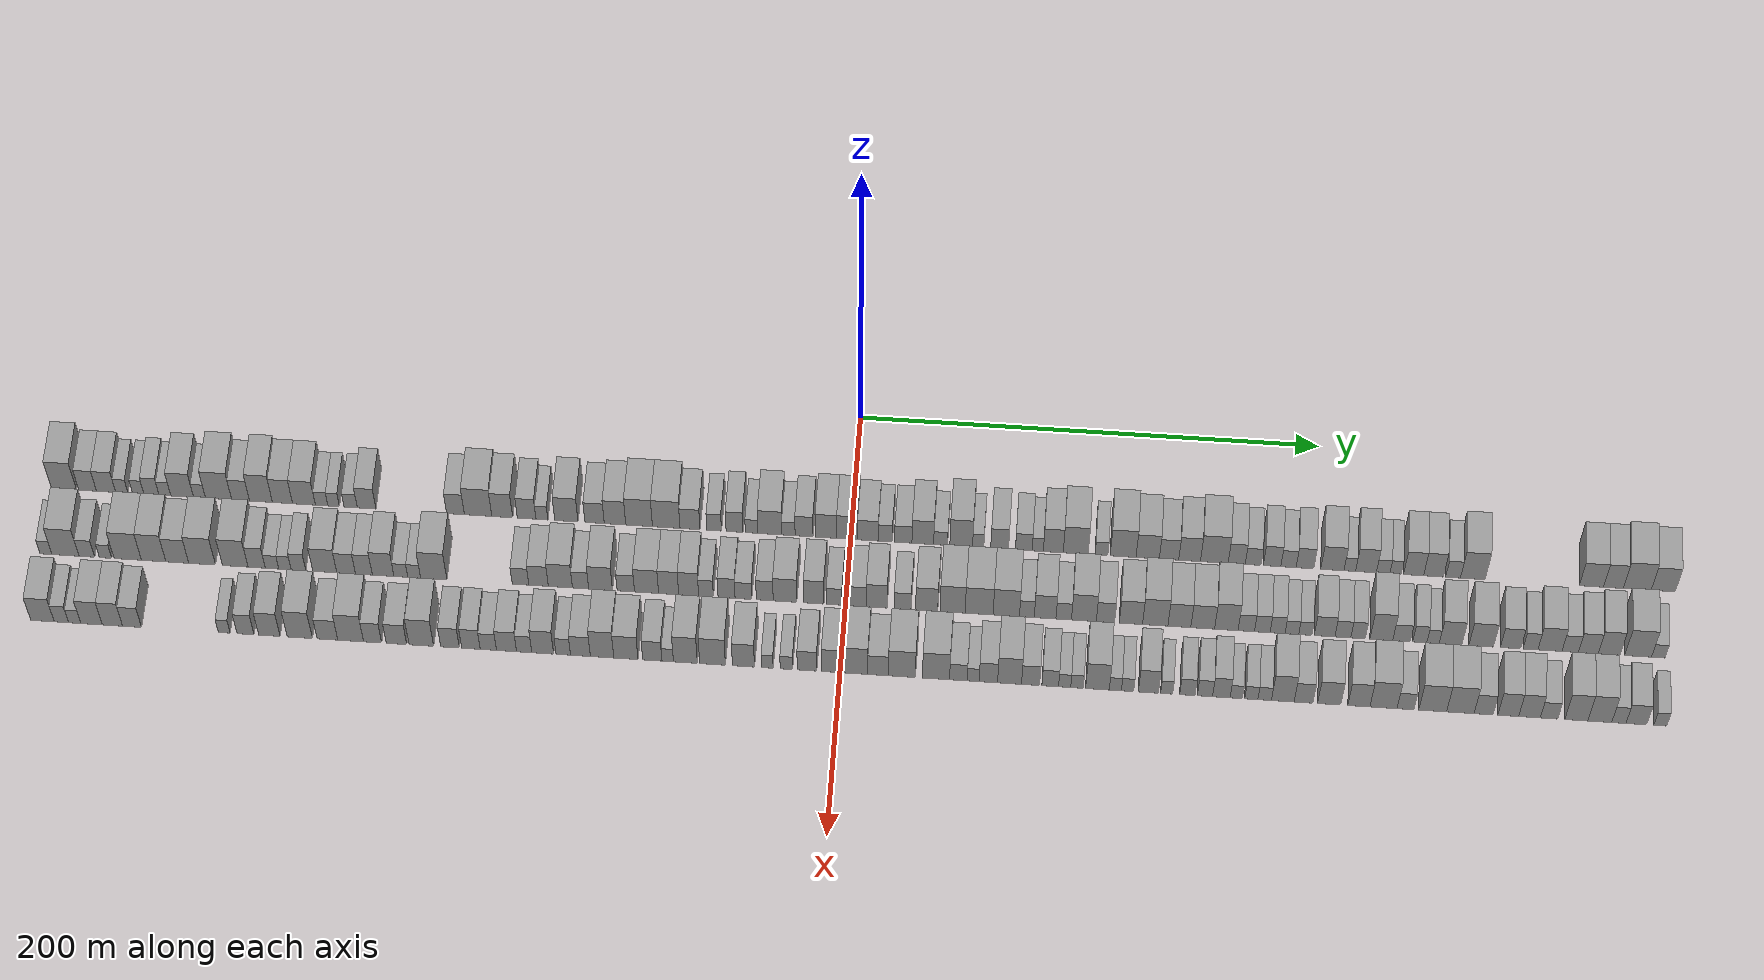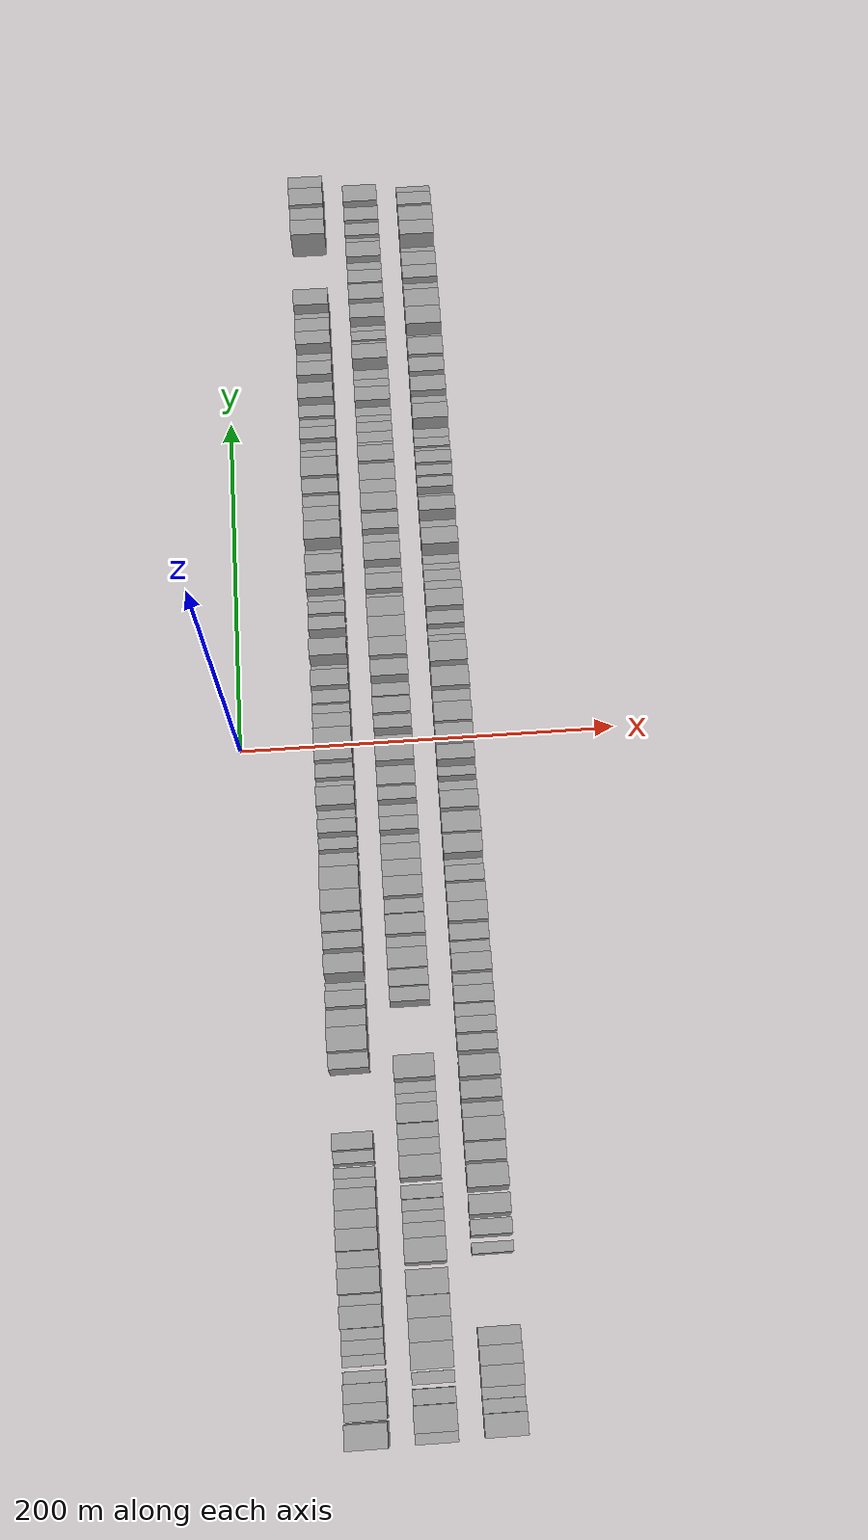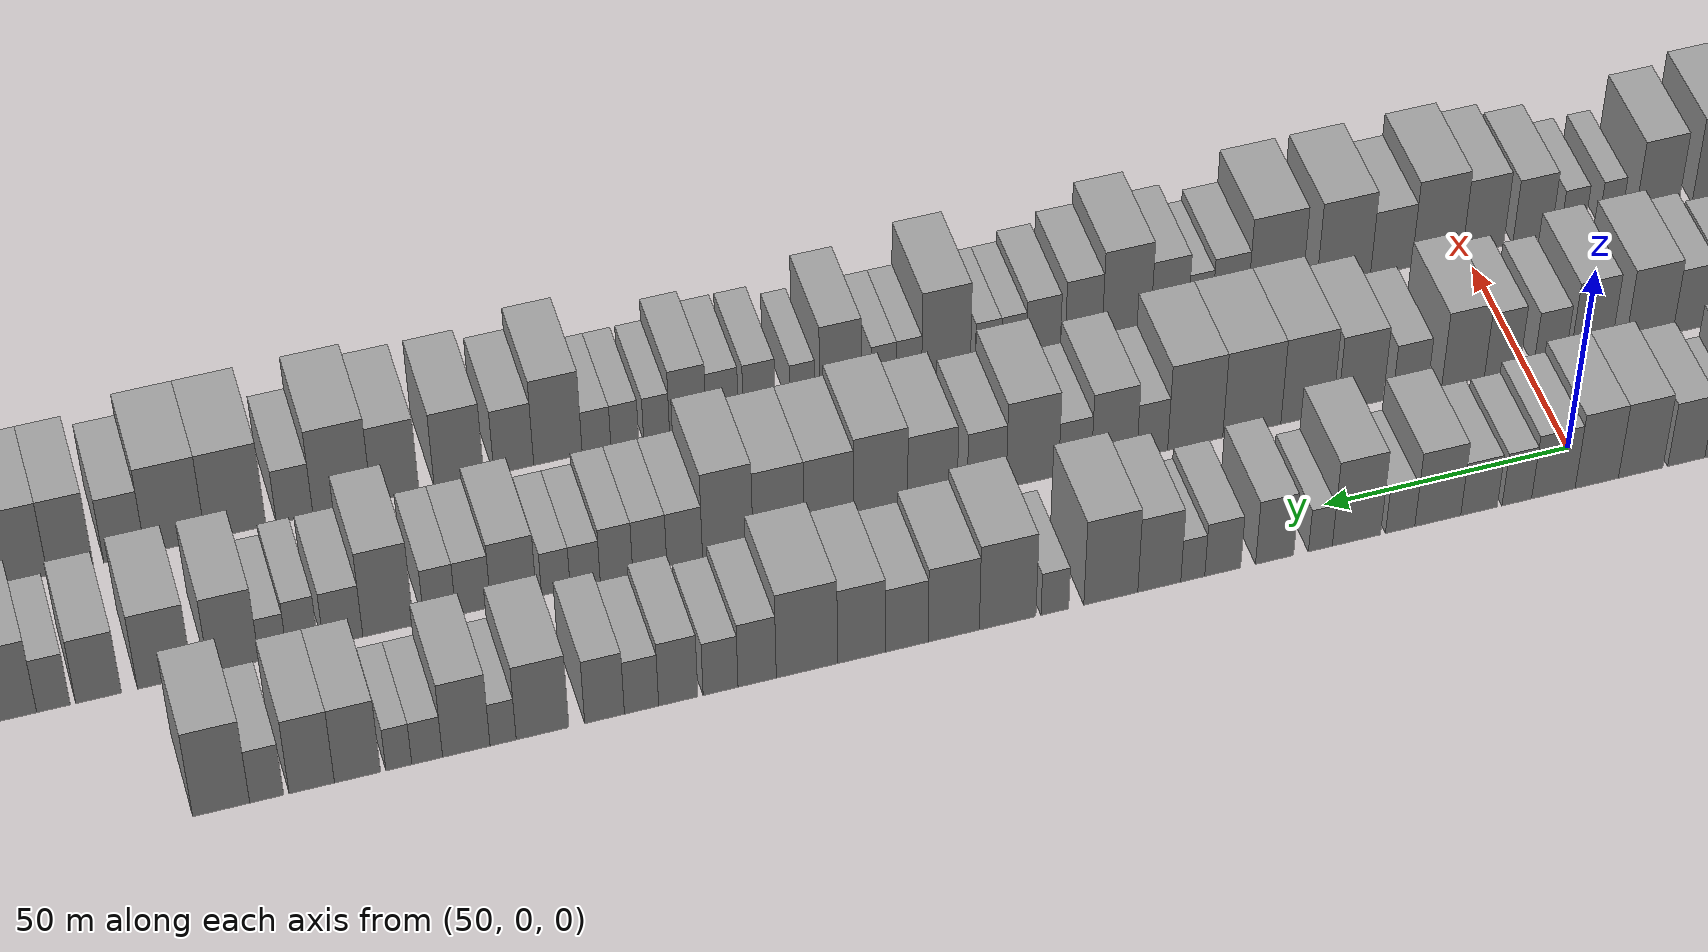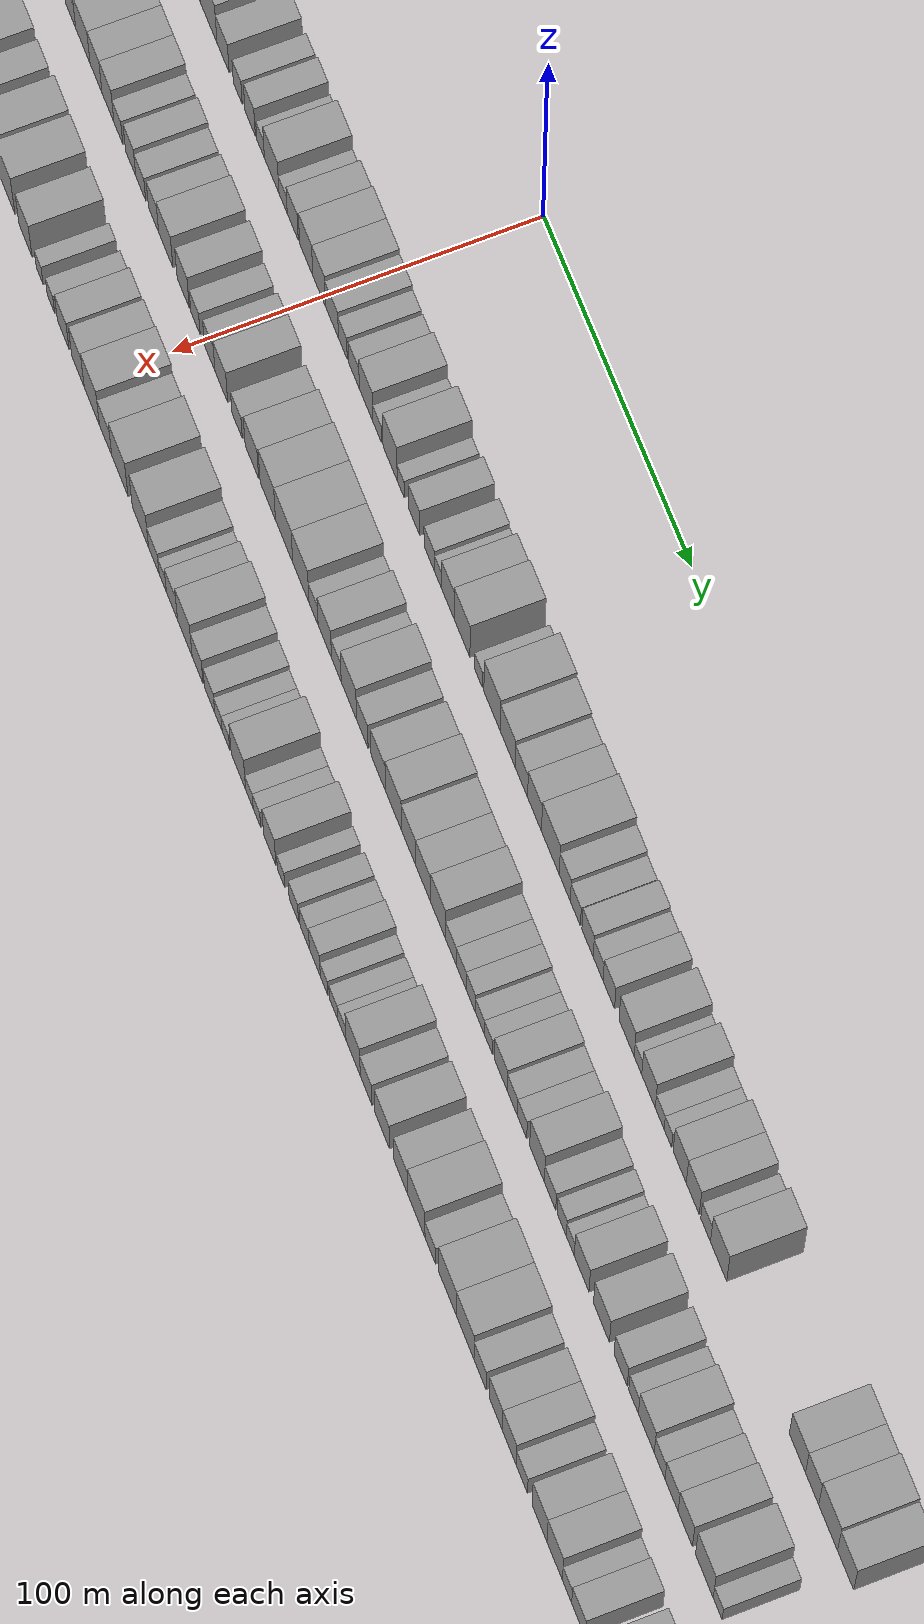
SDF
<sdf version="1.6">
 <world name="default">
  <scene>
   <sky><clouds><speed>12</speed></clouds></sky>
   <ambient>0.4 0.4 0.4 1</ambient>
   <background>0.7 0.7 0.7 1</background>
   <shadows>1</shadows>
  </scene>
  <gravity>0 0 -9.8066</gravity>
  <magnetic_field>6e-06 2.3e-05 -4.2e-05</magnetic_field>
  <physics default="0" name="default_physics" type="ode">
   <ode>
    <solver>
     <type>quick</type>
     <iters>10</iters>
     <sor>1.0</sor>
     <use_dynamic_moi_rescaling>0</use_dynamic_moi_rescaling>
    </solver>
    <constraints>
     <cfm>0</cfm>
     <erp>0.2</erp>
     <contact_max_correcting_vel>100</contact_max_correcting_vel>
     <contact_surface_layer>0.001</contact_surface_layer>
    </constraints>
   </ode>
   <max_step_size>0.004</max_step_size>
   <real_time_factor>1</real_time_factor>
   <real_time_update_rate>250</real_time_update_rate>
  </physics>
  <light name="sun" type="directional">
   <pose>0 0 10 0 0 0</pose>
   <diffuse>0.8 0.8 0.8 1</diffuse>
   <specular>0.2 0.2 0.2 1</specular>
   <attenuation>
    <range>1000</range>
    <constant>0.9</constant>
    <linear>0.01</linear>
    <quadratic>0.001</quadratic>
   </attenuation>
   <direction>-0.5 0.1 -0.9</direction>
  </light>
  <model name="building_1">
   <static>1</static>
   <pose>50.0000 -342.4957 0 0.000000 0.000000 0.000000</pose>
   <link name="link">
    <pose>0 0 12.00 0 0 0</pose>
    <collision name="collision"><geometry><box><size>20.0000 11.0086 24.0000</size></box></geometry></collision>
    <visual name="visual">
     <cast_shadows>0</cast_shadows>
     <geometry><box><size>20.0000 11.0086 24.0000</size></box></geometry>
     <material>
      <script>
       <uri>model://grey_wall/materials/scripts</uri>
       <uri>model://grey_wall/materials/textures</uri>
       <name>vrc/grey_wall</name>
      </script>
     </material>
    </visual>
   </link>
  </model>
  <model name="building_2">
   <static>1</static>
   <pose>50.0000 -332.1267 0 0.000000 0.000000 0.000000</pose>
   <link name="link">
    <pose>0 0 9.00 0 0 0</pose>
    <collision name="collision"><geometry><box><size>20.0000 7.7294 18.0000</size></box></geometry></collision>
    <visual name="visual">
     <cast_shadows>0</cast_shadows>
     <geometry><box><size>20.0000 7.7294 18.0000</size></box></geometry>
     <material>
      <script>
       <uri>model://grey_wall/materials/scripts</uri>
       <uri>model://grey_wall/materials/textures</uri>
       <name>vrc/grey_wall</name>
      </script>
     </material>
    </visual>
   </link>
  </model>
  <model name="building_3">
   <static>1</static>
   <pose>50.0000 -324.0537 0 0.000000 0.000000 0.000000</pose>
   <link name="link">
    <pose>0 0 9.00 0 0 0</pose>
    <collision name="collision"><geometry><box><size>20.0000 8.4165 18.0000</size></box></geometry></collision>
    <visual name="visual">
     <cast_shadows>0</cast_shadows>
     <geometry><box><size>20.0000 8.4165 18.0000</size></box></geometry>
     <material>
      <script>
       <uri>model://grey_wall/materials/scripts</uri>
       <uri>model://grey_wall/materials/textures</uri>
       <name>vrc/grey_wall</name>
      </script>
     </material>
    </visual>
   </link>
  </model>
  <model name="building_4">
   <static>1</static>
   <pose>50.0000 -317.1631 0 0.000000 0.000000 0.000000</pose>
   <link name="link">
    <pose>0 0 6.00 0 0 0</pose>
    <collision name="collision"><geometry><box><size>20.0000 5.3648 12.0000</size></box></geometry></collision>
    <visual name="visual">
     <cast_shadows>0</cast_shadows>
     <geometry><box><size>20.0000 5.3648 12.0000</size></box></geometry>
     <material>
      <script>
       <uri>model://grey_wall/materials/scripts</uri>
       <uri>model://grey_wall/materials/textures</uri>
       <name>vrc/grey_wall</name>
      </script>
     </material>
    </visual>
   </link>
  </model>
  <model name="building_5">
   <static>1</static>
   <pose>50.0000 -310.0044 0 0.000000 0.000000 0.000000</pose>
   <link name="link">
    <pose>0 0 6.00 0 0 0</pose>
    <collision name="collision"><geometry><box><size>20.0000 4.9525 12.0000</size></box></geometry></collision>
    <visual name="visual">
     <cast_shadows>0</cast_shadows>
     <geometry><box><size>20.0000 4.9525 12.0000</size></box></geometry>
     <material>
      <script>
       <uri>model://grey_wall/materials/scripts</uri>
       <uri>model://grey_wall/materials/textures</uri>
       <name>vrc/grey_wall</name>
      </script>
     </material>
    </visual>
   </link>
  </model>
  <model name="building_6">
   <static>1</static>
   <pose>50.0000 -304.2239 0 0.000000 0.000000 0.000000</pose>
   <link name="link">
    <pose>0 0 7.50 0 0 0</pose>
    <collision name="collision"><geometry><box><size>20.0000 6.6086 15.0000</size></box></geometry></collision>
    <visual name="visual">
     <cast_shadows>0</cast_shadows>
     <geometry><box><size>20.0000 6.6086 15.0000</size></box></geometry>
     <material>
      <script>
       <uri>model://grey_wall/materials/scripts</uri>
       <uri>model://grey_wall/materials/textures</uri>
       <name>vrc/grey_wall</name>
      </script>
     </material>
    </visual>
   </link>
  </model>
  <model name="building_7">
   <static>1</static>
   <pose>50.0000 -298.3457 0 0.000000 0.000000 0.000000</pose>
   <link name="link">
    <pose>0 0 6.00 0 0 0</pose>
    <collision name="collision"><geometry><box><size>20.0000 5.1477 12.0000</size></box></geometry></collision>
    <visual name="visual">
     <cast_shadows>0</cast_shadows>
     <geometry><box><size>20.0000 5.1477 12.0000</size></box></geometry>
     <material>
      <script>
       <uri>model://grey_wall/materials/scripts</uri>
       <uri>model://grey_wall/materials/textures</uri>
       <name>vrc/grey_wall</name>
      </script>
     </material>
    </visual>
   </link>
  </model>
  <model name="building_8">
   <static>1</static>
   <pose>50.0000 -290.8053 0 0.000000 0.000000 0.000000</pose>
   <link name="link">
    <pose>0 0 10.50 0 0 0</pose>
    <collision name="collision"><geometry><box><size>20.0000 9.9332 21.0000</size></box></geometry></collision>
    <visual name="visual">
     <cast_shadows>0</cast_shadows>
     <geometry><box><size>20.0000 9.9332 21.0000</size></box></geometry>
     <material>
      <script>
       <uri>model://grey_wall/materials/scripts</uri>
       <uri>model://grey_wall/materials/textures</uri>
       <name>vrc/grey_wall</name>
      </script>
     </material>
    </visual>
   </link>
  </model>
  <model name="building_9">
   <static>1</static>
   <pose>50.0000 -283.2354 0 0.000000 0.000000 0.000000</pose>
   <link name="link">
    <pose>0 0 6.00 0 0 0</pose>
    <collision name="collision"><geometry><box><size>20.0000 5.2066 12.0000</size></box></geometry></collision>
    <visual name="visual">
     <cast_shadows>0</cast_shadows>
     <geometry><box><size>20.0000 5.2066 12.0000</size></box></geometry>
     <material>
      <script>
       <uri>model://grey_wall/materials/scripts</uri>
       <uri>model://grey_wall/materials/textures</uri>
       <name>vrc/grey_wall</name>
      </script>
     </material>
    </visual>
   </link>
  </model>
  <model name="building_10">
   <static>1</static>
   <pose>50.0000 -274.9142 0 0.000000 0.000000 0.000000</pose>
   <link name="link">
    <pose>0 0 12.00 0 0 0</pose>
    <collision name="collision"><geometry><box><size>20.0000 11.4358 24.0000</size></box></geometry></collision>
    <visual name="visual">
     <cast_shadows>0</cast_shadows>
     <geometry><box><size>20.0000 11.4358 24.0000</size></box></geometry>
     <material>
      <script>
       <uri>model://grey_wall/materials/scripts</uri>
       <uri>model://grey_wall/materials/textures</uri>
       <name>vrc/grey_wall</name>
      </script>
     </material>
    </visual>
   </link>
  </model>
  <model name="building_11">
   <static>1</static>
   <pose>50.0000 -265.3020 0 0.000000 0.000000 0.000000</pose>
   <link name="link">
    <pose>0 0 9.00 0 0 0</pose>
    <collision name="collision"><geometry><box><size>20.0000 7.7885 18.0000</size></box></geometry></collision>
    <visual name="visual">
     <cast_shadows>0</cast_shadows>
     <geometry><box><size>20.0000 7.7885 18.0000</size></box></geometry>
     <material>
      <script>
       <uri>model://grey_wall/materials/scripts</uri>
       <uri>model://grey_wall/materials/textures</uri>
       <name>vrc/grey_wall</name>
      </script>
     </material>
    </visual>
   </link>
  </model>
  <model name="building_12">
   <static>1</static>
   <pose>50.0000 -256.4135 0 0.000000 0.000000 0.000000</pose>
   <link name="link">
    <pose>0 0 12.00 0 0 0</pose>
    <collision name="collision"><geometry><box><size>20.0000 9.9885 24.0000</size></box></geometry></collision>
    <visual name="visual">
     <cast_shadows>0</cast_shadows>
     <geometry><box><size>20.0000 9.9885 24.0000</size></box></geometry>
     <material>
      <script>
       <uri>model://grey_wall/materials/scripts</uri>
       <uri>model://grey_wall/materials/textures</uri>
       <name>vrc/grey_wall</name>
      </script>
     </material>
    </visual>
   </link>
  </model>
  <model name="building_13">
   <static>1</static>
   <pose>50.0000 -247.0191 0 0.000000 0.000000 0.000000</pose>
   <link name="link">
    <pose>0 0 10.50 0 0 0</pose>
    <collision name="collision"><geometry><box><size>20.0000 8.8004 21.0000</size></box></geometry></collision>
    <visual name="visual">
     <cast_shadows>0</cast_shadows>
     <geometry><box><size>20.0000 8.8004 21.0000</size></box></geometry>
     <material>
      <script>
       <uri>model://grey_wall/materials/scripts</uri>
       <uri>model://grey_wall/materials/textures</uri>
       <name>vrc/grey_wall</name>
      </script>
     </material>
    </visual>
   </link>
  </model>
  <model name="building_14">
   <static>1</static>
   <pose>50.0000 -237.6495 0 0.000000 0.000000 0.000000</pose>
   <link name="link">
    <pose>0 0 10.50 0 0 0</pose>
    <collision name="collision"><geometry><box><size>20.0000 9.9387 21.0000</size></box></geometry></collision>
    <visual name="visual">
     <cast_shadows>0</cast_shadows>
     <geometry><box><size>20.0000 9.9387 21.0000</size></box></geometry>
     <material>
      <script>
       <uri>model://grey_wall/materials/scripts</uri>
       <uri>model://grey_wall/materials/textures</uri>
       <name>vrc/grey_wall</name>
      </script>
     </material>
    </visual>
   </link>
  </model>
  <model name="building_15">
   <static>1</static>
   <pose>50.0000 -229.9502 0 0.000000 0.000000 0.000000</pose>
   <link name="link">
    <pose>0 0 6.00 0 0 0</pose>
    <collision name="collision"><geometry><box><size>20.0000 5.4601 12.0000</size></box></geometry></collision>
    <visual name="visual">
     <cast_shadows>0</cast_shadows>
     <geometry><box><size>20.0000 5.4601 12.0000</size></box></geometry>
     <material>
      <script>
       <uri>model://grey_wall/materials/scripts</uri>
       <uri>model://grey_wall/materials/textures</uri>
       <name>vrc/grey_wall</name>
      </script>
     </material>
    </visual>
   </link>
  </model>
  <model name="building_16">
   <static>1</static>
   <pose>50.0000 -224.7067 0 0.000000 0.000000 0.000000</pose>
   <link name="link">
    <pose>0 0 6.00 0 0 0</pose>
    <collision name="collision"><geometry><box><size>20.0000 5.0269 12.0000</size></box></geometry></collision>
    <visual name="visual">
     <cast_shadows>0</cast_shadows>
     <geometry><box><size>20.0000 5.0269 12.0000</size></box></geometry>
     <material>
      <script>
       <uri>model://grey_wall/materials/scripts</uri>
       <uri>model://grey_wall/materials/textures</uri>
       <name>vrc/grey_wall</name>
      </script>
     </material>
    </visual>
   </link>
  </model>
  <model name="building_17">
   <static>1</static>
   <pose>50.0000 -217.2980 0 0.000000 0.000000 0.000000</pose>
   <link name="link">
    <pose>0 0 6.00 0 0 0</pose>
    <collision name="collision"><geometry><box><size>20.0000 5.7905 12.0000</size></box></geometry></collision>
    <visual name="visual">
     <cast_shadows>0</cast_shadows>
     <geometry><box><size>20.0000 5.7905 12.0000</size></box></geometry>
     <material>
      <script>
       <uri>model://grey_wall/materials/scripts</uri>
       <uri>model://grey_wall/materials/textures</uri>
       <name>vrc/grey_wall</name>
      </script>
     </material>
    </visual>
   </link>
  </model>
  <model name="building_18">
   <static>1</static>
   <pose>50.0000 -210.3481 0 0.000000 0.000000 0.000000</pose>
   <link name="link">
    <pose>0 0 9.00 0 0 0</pose>
    <collision name="collision"><geometry><box><size>20.0000 8.1093 18.0000</size></box></geometry></collision>
    <visual name="visual">
     <cast_shadows>0</cast_shadows>
     <geometry><box><size>20.0000 8.1093 18.0000</size></box></geometry>
     <material>
      <script>
       <uri>model://grey_wall/materials/scripts</uri>
       <uri>model://grey_wall/materials/textures</uri>
       <name>vrc/grey_wall</name>
      </script>
     </material>
    </visual>
   </link>
  </model>
  <model name="building_19">
   <static>1</static>
   <pose>50.0000 -171.6649 0 0.000000 0.000000 0.000000</pose>
   <link name="link">
    <pose>0 0 9.00 0 0 0</pose>
    <collision name="collision"><geometry><box><size>20.0000 7.7523 18.0000</size></box></geometry></collision>
    <visual name="visual">
     <cast_shadows>0</cast_shadows>
     <geometry><box><size>20.0000 7.7523 18.0000</size></box></geometry>
     <material>
      <script>
       <uri>model://grey_wall/materials/scripts</uri>
       <uri>model://grey_wall/materials/textures</uri>
       <name>vrc/grey_wall</name>
      </script>
     </material>
    </visual>
   </link>
  </model>
  <model name="building_20">
   <static>1</static>
   <pose>50.0000 -161.8303 0 0.000000 0.000000 0.000000</pose>
   <link name="link">
    <pose>0 0 12.00 0 0 0</pose>
    <collision name="collision"><geometry><box><size>20.0000 11.9169 24.0000</size></box></geometry></collision>
    <visual name="visual">
     <cast_shadows>0</cast_shadows>
     <geometry><box><size>20.0000 11.9169 24.0000</size></box></geometry>
     <material>
      <script>
       <uri>model://grey_wall/materials/scripts</uri>
       <uri>model://grey_wall/materials/textures</uri>
       <name>vrc/grey_wall</name>
      </script>
     </material>
    </visual>
   </link>
  </model>
  <model name="building_21">
   <static>1</static>
   <pose>50.0000 -151.3336 0 0.000000 0.000000 0.000000</pose>
   <link name="link">
    <pose>0 0 10.50 0 0 0</pose>
    <collision name="collision"><geometry><box><size>20.0000 9.0767 21.0000</size></box></geometry></collision>
    <visual name="visual">
     <cast_shadows>0</cast_shadows>
     <geometry><box><size>20.0000 9.0767 21.0000</size></box></geometry>
     <material>
      <script>
       <uri>model://grey_wall/materials/scripts</uri>
       <uri>model://grey_wall/materials/textures</uri>
       <name>vrc/grey_wall</name>
      </script>
     </material>
    </visual>
   </link>
  </model>
  <model name="building_22">
   <static>1</static>
   <pose>50.0000 -140.7444 0 0.000000 0.000000 0.000000</pose>
   <link name="link">
    <pose>0 0 9.00 0 0 0</pose>
    <collision name="collision"><geometry><box><size>20.0000 8.1017 18.0000</size></box></geometry></collision>
    <visual name="visual">
     <cast_shadows>0</cast_shadows>
     <geometry><box><size>20.0000 8.1017 18.0000</size></box></geometry>
     <material>
      <script>
       <uri>model://grey_wall/materials/scripts</uri>
       <uri>model://grey_wall/materials/textures</uri>
       <name>vrc/grey_wall</name>
      </script>
     </material>
    </visual>
   </link>
  </model>
  <model name="building_23">
   <static>1</static>
   <pose>50.0000 -134.0986 0 0.000000 0.000000 0.000000</pose>
   <link name="link">
    <pose>0 0 6.00 0 0 0</pose>
    <collision name="collision"><geometry><box><size>20.0000 5.1899 12.0000</size></box></geometry></collision>
    <visual name="visual">
     <cast_shadows>0</cast_shadows>
     <geometry><box><size>20.0000 5.1899 12.0000</size></box></geometry>
     <material>
      <script>
       <uri>model://grey_wall/materials/scripts</uri>
       <uri>model://grey_wall/materials/textures</uri>
       <name>vrc/grey_wall</name>
      </script>
     </material>
    </visual>
   </link>
  </model>
  <model name="building_24">
   <static>1</static>
   <pose>50.0000 -123.4627 0 0.000000 0.000000 0.000000</pose>
   <link name="link">
    <pose>0 0 10.50 0 0 0</pose>
    <collision name="collision"><geometry><box><size>20.0000 10.0819 21.0000</size></box></geometry></collision>
    <visual name="visual">
     <cast_shadows>0</cast_shadows>
     <geometry><box><size>20.0000 10.0819 21.0000</size></box></geometry>
     <material>
      <script>
       <uri>model://grey_wall/materials/scripts</uri>
       <uri>model://grey_wall/materials/textures</uri>
       <name>vrc/grey_wall</name>
      </script>
     </material>
    </visual>
   </link>
  </model>
  <model name="building_25">
   <static>1</static>
   <pose>50.0000 -111.2321 0 0.000000 0.000000 0.000000</pose>
   <link name="link">
    <pose>0 0 9.00 0 0 0</pose>
    <collision name="collision"><geometry><box><size>20.0000 8.3793 18.0000</size></box></geometry></collision>
    <visual name="visual">
     <cast_shadows>0</cast_shadows>
     <geometry><box><size>20.0000 8.3793 18.0000</size></box></geometry>
     <material>
      <script>
       <uri>model://grey_wall/materials/scripts</uri>
       <uri>model://grey_wall/materials/textures</uri>
       <name>vrc/grey_wall</name>
      </script>
     </material>
    </visual>
   </link>
  </model>
  <model name="building_26">
   <static>1</static>
   <pose>50.0000 -102.3749 0 0.000000 0.000000 0.000000</pose>
   <link name="link">
    <pose>0 0 10.50 0 0 0</pose>
    <collision name="collision"><geometry><box><size>20.0000 9.3350 21.0000</size></box></geometry></collision>
    <visual name="visual">
     <cast_shadows>0</cast_shadows>
     <geometry><box><size>20.0000 9.3350 21.0000</size></box></geometry>
     <material>
      <script>
       <uri>model://grey_wall/materials/scripts</uri>
       <uri>model://grey_wall/materials/textures</uri>
       <name>vrc/grey_wall</name>
      </script>
     </material>
    </visual>
   </link>
  </model>
  <model name="building_27">
   <static>1</static>
   <pose>50.0000 -91.9184 0 0.000000 0.000000 0.000000</pose>
   <link name="link">
    <pose>0 0 12.00 0 0 0</pose>
    <collision name="collision"><geometry><box><size>20.0000 11.5780 24.0000</size></box></geometry></collision>
    <visual name="visual">
     <cast_shadows>0</cast_shadows>
     <geometry><box><size>20.0000 11.5780 24.0000</size></box></geometry>
     <material>
      <script>
       <uri>model://grey_wall/materials/scripts</uri>
       <uri>model://grey_wall/materials/textures</uri>
       <name>vrc/grey_wall</name>
      </script>
     </material>
    </visual>
   </link>
  </model>
  <model name="building_28">
   <static>1</static>
   <pose>50.0000 -80.1551 0 0.000000 0.000000 0.000000</pose>
   <link name="link">
    <pose>0 0 12.00 0 0 0</pose>
    <collision name="collision"><geometry><box><size>20.0000 11.9487 24.0000</size></box></geometry></collision>
    <visual name="visual">
     <cast_shadows>0</cast_shadows>
     <geometry><box><size>20.0000 11.9487 24.0000</size></box></geometry>
     <material>
      <script>
       <uri>model://grey_wall/materials/scripts</uri>
       <uri>model://grey_wall/materials/textures</uri>
       <name>vrc/grey_wall</name>
      </script>
     </material>
    </visual>
   </link>
  </model>
  <model name="building_29">
   <static>1</static>
   <pose>50.0000 -69.8489 0 0.000000 0.000000 0.000000</pose>
   <link name="link">
    <pose>0 0 9.00 0 0 0</pose>
    <collision name="collision"><geometry><box><size>20.0000 8.6638 18.0000</size></box></geometry></collision>
    <visual name="visual">
     <cast_shadows>0</cast_shadows>
     <geometry><box><size>20.0000 8.6638 18.0000</size></box></geometry>
     <material>
      <script>
       <uri>model://grey_wall/materials/scripts</uri>
       <uri>model://grey_wall/materials/textures</uri>
       <name>vrc/grey_wall</name>
      </script>
     </material>
    </visual>
   </link>
  </model>
  <model name="building_30">
   <static>1</static>
   <pose>50.0000 -59.3672 0 0.000000 0.000000 0.000000</pose>
   <link name="link">
    <pose>0 0 7.50 0 0 0</pose>
    <collision name="collision"><geometry><box><size>20.0000 6.2996 15.0000</size></box></geometry></collision>
    <visual name="visual">
     <cast_shadows>0</cast_shadows>
     <geometry><box><size>20.0000 6.2996 15.0000</size></box></geometry>
     <material>
      <script>
       <uri>model://grey_wall/materials/scripts</uri>
       <uri>model://grey_wall/materials/textures</uri>
       <name>vrc/grey_wall</name>
      </script>
     </material>
    </visual>
   </link>
  </model>
  <model name="building_31">
   <static>1</static>
   <pose>50.0000 -50.5570 0 0.000000 0.000000 0.000000</pose>
   <link name="link">
    <pose>0 0 9.00 0 0 0</pose>
    <collision name="collision"><geometry><box><size>20.0000 7.3209 18.0000</size></box></geometry></collision>
    <visual name="visual">
     <cast_shadows>0</cast_shadows>
     <geometry><box><size>20.0000 7.3209 18.0000</size></box></geometry>
     <material>
      <script>
       <uri>model://grey_wall/materials/scripts</uri>
       <uri>model://grey_wall/materials/textures</uri>
       <name>vrc/grey_wall</name>
      </script>
     </material>
    </visual>
   </link>
  </model>
  <model name="building_32">
   <static>1</static>
   <pose>50.0000 -43.1725 0 0.000000 0.000000 0.000000</pose>
   <link name="link">
    <pose>0 0 6.00 0 0 0</pose>
    <collision name="collision"><geometry><box><size>20.0000 5.4480 12.0000</size></box></geometry></collision>
    <visual name="visual">
     <cast_shadows>0</cast_shadows>
     <geometry><box><size>20.0000 5.4480 12.0000</size></box></geometry>
     <material>
      <script>
       <uri>model://grey_wall/materials/scripts</uri>
       <uri>model://grey_wall/materials/textures</uri>
       <name>vrc/grey_wall</name>
      </script>
     </material>
    </visual>
   </link>
  </model>
  <model name="building_33">
   <static>1</static>
   <pose>50.0000 -35.2940 0 0.000000 0.000000 0.000000</pose>
   <link name="link">
    <pose>0 0 10.50 0 0 0</pose>
    <collision name="collision"><geometry><box><size>20.0000 10.3091 21.0000</size></box></geometry></collision>
    <visual name="visual">
     <cast_shadows>0</cast_shadows>
     <geometry><box><size>20.0000 10.3091 21.0000</size></box></geometry>
     <material>
      <script>
       <uri>model://grey_wall/materials/scripts</uri>
       <uri>model://grey_wall/materials/textures</uri>
       <name>vrc/grey_wall</name>
      </script>
     </material>
    </visual>
   </link>
  </model>
  <model name="building_34">
   <static>1</static>
   <pose>50.0000 -27.2335 0 0.000000 0.000000 0.000000</pose>
   <link name="link">
    <pose>0 0 6.00 0 0 0</pose>
    <collision name="collision"><geometry><box><size>20.0000 5.8118 12.0000</size></box></geometry></collision>
    <visual name="visual">
     <cast_shadows>0</cast_shadows>
     <geometry><box><size>20.0000 5.8118 12.0000</size></box></geometry>
     <material>
      <script>
       <uri>model://grey_wall/materials/scripts</uri>
       <uri>model://grey_wall/materials/textures</uri>
       <name>vrc/grey_wall</name>
      </script>
     </material>
    </visual>
   </link>
  </model>
  <model name="building_35">
   <static>1</static>
   <pose>50.0000 -20.4533 0 0.000000 0.000000 0.000000</pose>
   <link name="link">
    <pose>0 0 9.00 0 0 0</pose>
    <collision name="collision"><geometry><box><size>20.0000 7.7486 18.0000</size></box></geometry></collision>
    <visual name="visual">
     <cast_shadows>0</cast_shadows>
     <geometry><box><size>20.0000 7.7486 18.0000</size></box></geometry>
     <material>
      <script>
       <uri>model://grey_wall/materials/scripts</uri>
       <uri>model://grey_wall/materials/textures</uri>
       <name>vrc/grey_wall</name>
      </script>
     </material>
    </visual>
   </link>
  </model>
  <model name="building_36">
   <static>1</static>
   <pose>50.0000 -10.9600 0 0.000000 0.000000 0.000000</pose>
   <link name="link">
    <pose>0 0 10.50 0 0 0</pose>
    <collision name="collision"><geometry><box><size>20.0000 9.2382 21.0000</size></box></geometry></collision>
    <visual name="visual">
     <cast_shadows>0</cast_shadows>
     <geometry><box><size>20.0000 9.2382 21.0000</size></box></geometry>
     <material>
      <script>
       <uri>model://grey_wall/materials/scripts</uri>
       <uri>model://grey_wall/materials/textures</uri>
       <name>vrc/grey_wall</name>
      </script>
     </material>
    </visual>
   </link>
  </model>
  <model name="building_37">
   <static>1</static>
   <pose>50.0000 -1.8528 0 0.000000 0.000000 0.000000</pose>
   <link name="link">
    <pose>0 0 10.50 0 0 0</pose>
    <collision name="collision"><geometry><box><size>20.0000 8.9762 21.0000</size></box></geometry></collision>
    <visual name="visual">
     <cast_shadows>0</cast_shadows>
     <geometry><box><size>20.0000 8.9762 21.0000</size></box></geometry>
     <material>
      <script>
       <uri>model://grey_wall/materials/scripts</uri>
       <uri>model://grey_wall/materials/textures</uri>
       <name>vrc/grey_wall</name>
      </script>
     </material>
    </visual>
   </link>
  </model>
  <model name="building_38">
   <static>1</static>
   <pose>50.0000 7.1288 0 0.000000 0.000000 0.000000</pose>
   <link name="link">
    <pose>0 0 9.00 0 0 0</pose>
    <collision name="collision"><geometry><box><size>20.0000 8.9869 18.0000</size></box></geometry></collision>
    <visual name="visual">
     <cast_shadows>0</cast_shadows>
     <geometry><box><size>20.0000 8.9869 18.0000</size></box></geometry>
     <material>
      <script>
       <uri>model://grey_wall/materials/scripts</uri>
       <uri>model://grey_wall/materials/textures</uri>
       <name>vrc/grey_wall</name>
      </script>
     </material>
    </visual>
   </link>
  </model>
  <model name="building_39">
   <static>1</static>
   <pose>50.0000 14.6625 0 0.000000 0.000000 0.000000</pose>
   <link name="link">
    <pose>0 0 7.50 0 0 0</pose>
    <collision name="collision"><geometry><box><size>20.0000 6.0806 15.0000</size></box></geometry></collision>
    <visual name="visual">
     <cast_shadows>0</cast_shadows>
     <geometry><box><size>20.0000 6.0806 15.0000</size></box></geometry>
     <material>
      <script>
       <uri>model://grey_wall/materials/scripts</uri>
       <uri>model://grey_wall/materials/textures</uri>
       <name>vrc/grey_wall</name>
      </script>
     </material>
    </visual>
   </link>
  </model>
  <model name="building_40">
   <static>1</static>
   <pose>50.0000 22.4409 0 0.000000 0.000000 0.000000</pose>
   <link name="link">
    <pose>0 0 7.50 0 0 0</pose>
    <collision name="collision"><geometry><box><size>20.0000 7.4761 15.0000</size></box></geometry></collision>
    <visual name="visual">
     <cast_shadows>0</cast_shadows>
     <geometry><box><size>20.0000 7.4761 15.0000</size></box></geometry>
     <material>
      <script>
       <uri>model://grey_wall/materials/scripts</uri>
       <uri>model://grey_wall/materials/textures</uri>
       <name>vrc/grey_wall</name>
      </script>
     </material>
    </visual>
   </link>
  </model>
  <model name="building_41">
   <static>1</static>
   <pose>50.0000 30.8752 0 0.000000 0.000000 0.000000</pose>
   <link name="link">
    <pose>0 0 10.50 0 0 0</pose>
    <collision name="collision"><geometry><box><size>20.0000 9.3926 21.0000</size></box></geometry></collision>
    <visual name="visual">
     <cast_shadows>0</cast_shadows>
     <geometry><box><size>20.0000 9.3926 21.0000</size></box></geometry>
     <material>
      <script>
       <uri>model://grey_wall/materials/scripts</uri>
       <uri>model://grey_wall/materials/textures</uri>
       <name>vrc/grey_wall</name>
      </script>
     </material>
    </visual>
   </link>
  </model>
  <model name="building_42">
   <static>1</static>
   <pose>50.0000 38.5648 0 0.000000 0.000000 0.000000</pose>
   <link name="link">
    <pose>0 0 6.00 0 0 0</pose>
    <collision name="collision"><geometry><box><size>20.0000 5.9864 12.0000</size></box></geometry></collision>
    <visual name="visual">
     <cast_shadows>0</cast_shadows>
     <geometry><box><size>20.0000 5.9864 12.0000</size></box></geometry>
     <material>
      <script>
       <uri>model://grey_wall/materials/scripts</uri>
       <uri>model://grey_wall/materials/textures</uri>
       <name>vrc/grey_wall</name>
      </script>
     </material>
    </visual>
   </link>
  </model>
  <model name="building_43">
   <static>1</static>
   <pose>50.0000 47.4560 0 0.000000 0.000000 0.000000</pose>
   <link name="link">
    <pose>0 0 12.00 0 0 0</pose>
    <collision name="collision"><geometry><box><size>20.0000 9.7959 24.0000</size></box></geometry></collision>
    <visual name="visual">
     <cast_shadows>0</cast_shadows>
     <geometry><box><size>20.0000 9.7959 24.0000</size></box></geometry>
     <material>
      <script>
       <uri>model://grey_wall/materials/scripts</uri>
       <uri>model://grey_wall/materials/textures</uri>
       <name>vrc/grey_wall</name>
      </script>
     </material>
    </visual>
   </link>
  </model>
  <model name="building_44">
   <static>1</static>
   <pose>50.0000 54.7736 0 0.000000 0.000000 0.000000</pose>
   <link name="link">
    <pose>0 0 6.00 0 0 0</pose>
    <collision name="collision"><geometry><box><size>20.0000 4.8394 12.0000</size></box></geometry></collision>
    <visual name="visual">
     <cast_shadows>0</cast_shadows>
     <geometry><box><size>20.0000 4.8394 12.0000</size></box></geometry>
     <material>
      <script>
       <uri>model://grey_wall/materials/scripts</uri>
       <uri>model://grey_wall/materials/textures</uri>
       <name>vrc/grey_wall</name>
      </script>
     </material>
    </visual>
   </link>
  </model>
  <model name="building_45">
   <static>1</static>
   <pose>50.0000 64.0287 0 0.000000 0.000000 0.000000</pose>
   <link name="link">
    <pose>0 0 9.00 0 0 0</pose>
    <collision name="collision"><geometry><box><size>20.0000 7.6707 18.0000</size></box></geometry></collision>
    <visual name="visual">
     <cast_shadows>0</cast_shadows>
     <geometry><box><size>20.0000 7.6707 18.0000</size></box></geometry>
     <material>
      <script>
       <uri>model://grey_wall/materials/scripts</uri>
       <uri>model://grey_wall/materials/textures</uri>
       <name>vrc/grey_wall</name>
      </script>
     </material>
    </visual>
   </link>
  </model>
  <model name="building_46">
   <static>1</static>
   <pose>50.0000 74.4639 0 0.000000 0.000000 0.000000</pose>
   <link name="link">
    <pose>0 0 7.50 0 0 0</pose>
    <collision name="collision"><geometry><box><size>20.0000 7.1998 15.0000</size></box></geometry></collision>
    <visual name="visual">
     <cast_shadows>0</cast_shadows>
     <geometry><box><size>20.0000 7.1998 15.0000</size></box></geometry>
     <material>
      <script>
       <uri>model://grey_wall/materials/scripts</uri>
       <uri>model://grey_wall/materials/textures</uri>
       <name>vrc/grey_wall</name>
      </script>
     </material>
    </visual>
   </link>
  </model>
  <model name="building_47">
   <static>1</static>
   <pose>50.0000 80.4667 0 0.000000 0.000000 0.000000</pose>
   <link name="link">
    <pose>0 0 6.00 0 0 0</pose>
    <collision name="collision"><geometry><box><size>20.0000 4.8058 12.0000</size></box></geometry></collision>
    <visual name="visual">
     <cast_shadows>0</cast_shadows>
     <geometry><box><size>20.0000 4.8058 12.0000</size></box></geometry>
     <material>
      <script>
       <uri>model://grey_wall/materials/scripts</uri>
       <uri>model://grey_wall/materials/textures</uri>
       <name>vrc/grey_wall</name>
      </script>
     </material>
    </visual>
   </link>
  </model>
  <model name="building_48">
   <static>1</static>
   <pose>50.0000 87.1606 0 0.000000 0.000000 0.000000</pose>
   <link name="link">
    <pose>0 0 10.50 0 0 0</pose>
    <collision name="collision"><geometry><box><size>20.0000 8.5819 21.0000</size></box></geometry></collision>
    <visual name="visual">
     <cast_shadows>0</cast_shadows>
     <geometry><box><size>20.0000 8.5819 21.0000</size></box></geometry>
     <material>
      <script>
       <uri>model://grey_wall/materials/scripts</uri>
       <uri>model://grey_wall/materials/textures</uri>
       <name>vrc/grey_wall</name>
      </script>
     </material>
    </visual>
   </link>
  </model>
  <model name="building_49">
   <static>1</static>
   <pose>50.0000 96.8228 0 0.000000 0.000000 0.000000</pose>
   <link name="link">
    <pose>0 0 12.00 0 0 0</pose>
    <collision name="collision"><geometry><box><size>20.0000 10.7425 24.0000</size></box></geometry></collision>
    <visual name="visual">
     <cast_shadows>0</cast_shadows>
     <geometry><box><size>20.0000 10.7425 24.0000</size></box></geometry>
     <material>
      <script>
       <uri>model://grey_wall/materials/scripts</uri>
       <uri>model://grey_wall/materials/textures</uri>
       <name>vrc/grey_wall</name>
      </script>
     </material>
    </visual>
   </link>
  </model>
  <model name="building_50">
   <static>1</static>
   <pose>50.0000 107.9392 0 0.000000 0.000000 0.000000</pose>
   <link name="link">
    <pose>0 0 6.00 0 0 0</pose>
    <collision name="collision"><geometry><box><size>20.0000 5.4903 12.0000</size></box></geometry></collision>
    <visual name="visual">
     <cast_shadows>0</cast_shadows>
     <geometry><box><size>20.0000 5.4903 12.0000</size></box></geometry>
     <material>
      <script>
       <uri>model://grey_wall/materials/scripts</uri>
       <uri>model://grey_wall/materials/textures</uri>
       <name>vrc/grey_wall</name>
      </script>
     </material>
    </visual>
   </link>
  </model>
  <model name="building_51">
   <static>1</static>
   <pose>50.0000 117.2635 0 0.000000 0.000000 0.000000</pose>
   <link name="link">
    <pose>0 0 12.00 0 0 0</pose>
    <collision name="collision"><geometry><box><size>20.0000 11.1584 24.0000</size></box></geometry></collision>
    <visual name="visual">
     <cast_shadows>0</cast_shadows>
     <geometry><box><size>20.0000 11.1584 24.0000</size></box></geometry>
     <material>
      <script>
       <uri>model://grey_wall/materials/scripts</uri>
       <uri>model://grey_wall/materials/textures</uri>
       <name>vrc/grey_wall</name>
      </script>
     </material>
    </visual>
   </link>
  </model>
  <model name="building_52">
   <static>1</static>
   <pose>50.0000 127.8642 0 0.000000 0.000000 0.000000</pose>
   <link name="link">
    <pose>0 0 10.50 0 0 0</pose>
    <collision name="collision"><geometry><box><size>20.0000 10.0431 21.0000</size></box></geometry></collision>
    <visual name="visual">
     <cast_shadows>0</cast_shadows>
     <geometry><box><size>20.0000 10.0431 21.0000</size></box></geometry>
     <material>
      <script>
       <uri>model://grey_wall/materials/scripts</uri>
       <uri>model://grey_wall/materials/textures</uri>
       <name>vrc/grey_wall</name>
      </script>
     </material>
    </visual>
   </link>
  </model>
  <model name="building_53">
   <static>1</static>
   <pose>50.0000 137.0597 0 0.000000 0.000000 0.000000</pose>
   <link name="link">
    <pose>0 0 9.00 0 0 0</pose>
    <collision name="collision"><geometry><box><size>20.0000 8.3479 18.0000</size></box></geometry></collision>
    <visual name="visual">
     <cast_shadows>0</cast_shadows>
     <geometry><box><size>20.0000 8.3479 18.0000</size></box></geometry>
     <material>
      <script>
       <uri>model://grey_wall/materials/scripts</uri>
       <uri>model://grey_wall/materials/textures</uri>
       <name>vrc/grey_wall</name>
      </script>
     </material>
    </visual>
   </link>
  </model>
  <model name="building_54">
   <static>1</static>
   <pose>50.0000 145.9074 0 0.000000 0.000000 0.000000</pose>
   <link name="link">
    <pose>0 0 10.50 0 0 0</pose>
    <collision name="collision"><geometry><box><size>20.0000 9.3477 21.0000</size></box></geometry></collision>
    <visual name="visual">
     <cast_shadows>0</cast_shadows>
     <geometry><box><size>20.0000 9.3477 21.0000</size></box></geometry>
     <material>
      <script>
       <uri>model://grey_wall/materials/scripts</uri>
       <uri>model://grey_wall/materials/textures</uri>
       <name>vrc/grey_wall</name>
      </script>
     </material>
    </visual>
   </link>
  </model>
  <model name="building_55">
   <static>1</static>
   <pose>50.0000 156.5273 0 0.000000 0.000000 0.000000</pose>
   <link name="link">
    <pose>0 0 12.00 0 0 0</pose>
    <collision name="collision"><geometry><box><size>20.0000 11.8921 24.0000</size></box></geometry></collision>
    <visual name="visual">
     <cast_shadows>0</cast_shadows>
     <geometry><box><size>20.0000 11.8921 24.0000</size></box></geometry>
     <material>
      <script>
       <uri>model://grey_wall/materials/scripts</uri>
       <uri>model://grey_wall/materials/textures</uri>
       <name>vrc/grey_wall</name>
      </script>
     </material>
    </visual>
   </link>
  </model>
  <model name="building_56">
   <static>1</static>
   <pose>50.0000 166.1714 0 0.000000 0.000000 0.000000</pose>
   <link name="link">
    <pose>0 0 9.00 0 0 0</pose>
    <collision name="collision"><geometry><box><size>20.0000 7.3960 18.0000</size></box></geometry></collision>
    <visual name="visual">
     <cast_shadows>0</cast_shadows>
     <geometry><box><size>20.0000 7.3960 18.0000</size></box></geometry>
     <material>
      <script>
       <uri>model://grey_wall/materials/scripts</uri>
       <uri>model://grey_wall/materials/textures</uri>
       <name>vrc/grey_wall</name>
      </script>
     </material>
    </visual>
   </link>
  </model>
  <model name="building_57">
   <static>1</static>
   <pose>50.0000 173.2329 0 0.000000 0.000000 0.000000</pose>
   <link name="link">
    <pose>0 0 7.50 0 0 0</pose>
    <collision name="collision"><geometry><box><size>20.0000 6.7270 15.0000</size></box></geometry></collision>
    <visual name="visual">
     <cast_shadows>0</cast_shadows>
     <geometry><box><size>20.0000 6.7270 15.0000</size></box></geometry>
     <material>
      <script>
       <uri>model://grey_wall/materials/scripts</uri>
       <uri>model://grey_wall/materials/textures</uri>
       <name>vrc/grey_wall</name>
      </script>
     </material>
    </visual>
   </link>
  </model>
  <model name="building_58">
   <static>1</static>
   <pose>50.0000 181.3587 0 0.000000 0.000000 0.000000</pose>
   <link name="link">
    <pose>0 0 9.00 0 0 0</pose>
    <collision name="collision"><geometry><box><size>20.0000 7.5245 18.0000</size></box></geometry></collision>
    <visual name="visual">
     <cast_shadows>0</cast_shadows>
     <geometry><box><size>20.0000 7.5245 18.0000</size></box></geometry>
     <material>
      <script>
       <uri>model://grey_wall/materials/scripts</uri>
       <uri>model://grey_wall/materials/textures</uri>
       <name>vrc/grey_wall</name>
      </script>
     </material>
    </visual>
   </link>
  </model>
  <model name="building_59">
   <static>1</static>
   <pose>50.0000 188.4044 0 0.000000 0.000000 0.000000</pose>
   <link name="link">
    <pose>0 0 7.50 0 0 0</pose>
    <collision name="collision"><geometry><box><size>20.0000 6.5669 15.0000</size></box></geometry></collision>
    <visual name="visual">
     <cast_shadows>0</cast_shadows>
     <geometry><box><size>20.0000 6.5669 15.0000</size></box></geometry>
     <material>
      <script>
       <uri>model://grey_wall/materials/scripts</uri>
       <uri>model://grey_wall/materials/textures</uri>
       <name>vrc/grey_wall</name>
      </script>
     </material>
    </visual>
   </link>
  </model>
  <model name="building_60">
   <static>1</static>
   <pose>50.0000 195.4860 0 0.000000 0.000000 0.000000</pose>
   <link name="link">
    <pose>0 0 9.00 0 0 0</pose>
    <collision name="collision"><geometry><box><size>20.0000 7.5963 18.0000</size></box></geometry></collision>
    <visual name="visual">
     <cast_shadows>0</cast_shadows>
     <geometry><box><size>20.0000 7.5963 18.0000</size></box></geometry>
     <material>
      <script>
       <uri>model://grey_wall/materials/scripts</uri>
       <uri>model://grey_wall/materials/textures</uri>
       <name>vrc/grey_wall</name>
      </script>
     </material>
    </visual>
   </link>
  </model>
  <model name="building_61">
   <static>1</static>
   <pose>50.0000 207.2871 0 0.000000 0.000000 0.000000</pose>
   <link name="link">
    <pose>0 0 10.50 0 0 0</pose>
    <collision name="collision"><geometry><box><size>20.0000 10.0059 21.0000</size></box></geometry></collision>
    <visual name="visual">
     <cast_shadows>0</cast_shadows>
     <geometry><box><size>20.0000 10.0059 21.0000</size></box></geometry>
     <material>
      <script>
       <uri>model://grey_wall/materials/scripts</uri>
       <uri>model://grey_wall/materials/textures</uri>
       <name>vrc/grey_wall</name>
      </script>
     </material>
    </visual>
   </link>
  </model>
  <model name="building_62">
   <static>1</static>
   <pose>50.0000 214.7658 0 0.000000 0.000000 0.000000</pose>
   <link name="link">
    <pose>0 0 6.00 0 0 0</pose>
    <collision name="collision"><geometry><box><size>20.0000 4.9516 12.0000</size></box></geometry></collision>
    <visual name="visual">
     <cast_shadows>0</cast_shadows>
     <geometry><box><size>20.0000 4.9516 12.0000</size></box></geometry>
     <material>
      <script>
       <uri>model://grey_wall/materials/scripts</uri>
       <uri>model://grey_wall/materials/textures</uri>
       <name>vrc/grey_wall</name>
      </script>
     </material>
    </visual>
   </link>
  </model>
  <model name="building_63">
   <static>1</static>
   <pose>50.0000 221.7209 0 0.000000 0.000000 0.000000</pose>
   <link name="link">
    <pose>0 0 10.50 0 0 0</pose>
    <collision name="collision"><geometry><box><size>20.0000 8.9585 21.0000</size></box></geometry></collision>
    <visual name="visual">
     <cast_shadows>0</cast_shadows>
     <geometry><box><size>20.0000 8.9585 21.0000</size></box></geometry>
     <material>
      <script>
       <uri>model://grey_wall/materials/scripts</uri>
       <uri>model://grey_wall/materials/textures</uri>
       <name>vrc/grey_wall</name>
      </script>
     </material>
    </visual>
   </link>
  </model>
  <model name="building_64">
   <static>1</static>
   <pose>50.0000 229.0972 0 0.000000 0.000000 0.000000</pose>
   <link name="link">
    <pose>0 0 6.00 0 0 0</pose>
    <collision name="collision"><geometry><box><size>20.0000 5.7941 12.0000</size></box></geometry></collision>
    <visual name="visual">
     <cast_shadows>0</cast_shadows>
     <geometry><box><size>20.0000 5.7941 12.0000</size></box></geometry>
     <material>
      <script>
       <uri>model://grey_wall/materials/scripts</uri>
       <uri>model://grey_wall/materials/textures</uri>
       <name>vrc/grey_wall</name>
      </script>
     </material>
    </visual>
   </link>
  </model>
  <model name="building_65">
   <static>1</static>
   <pose>50.0000 234.4297 0 0.000000 0.000000 0.000000</pose>
   <link name="link">
    <pose>0 0 6.00 0 0 0</pose>
    <collision name="collision"><geometry><box><size>20.0000 4.8709 12.0000</size></box></geometry></collision>
    <visual name="visual">
     <cast_shadows>0</cast_shadows>
     <geometry><box><size>20.0000 4.8709 12.0000</size></box></geometry>
     <material>
      <script>
       <uri>model://grey_wall/materials/scripts</uri>
       <uri>model://grey_wall/materials/textures</uri>
       <name>vrc/grey_wall</name>
      </script>
     </material>
    </visual>
   </link>
  </model>
  <model name="building_66">
   <static>1</static>
   <pose>50.0000 242.1721 0 0.000000 0.000000 0.000000</pose>
   <link name="link">
    <pose>0 0 10.50 0 0 0</pose>
    <collision name="collision"><geometry><box><size>20.0000 8.6137 21.0000</size></box></geometry></collision>
    <visual name="visual">
     <cast_shadows>0</cast_shadows>
     <geometry><box><size>20.0000 8.6137 21.0000</size></box></geometry>
     <material>
      <script>
       <uri>model://grey_wall/materials/scripts</uri>
       <uri>model://grey_wall/materials/textures</uri>
       <name>vrc/grey_wall</name>
      </script>
     </material>
    </visual>
   </link>
  </model>
  <model name="building_67">
   <static>1</static>
   <pose>50.0000 250.7116 0 0.000000 0.000000 0.000000</pose>
   <link name="link">
    <pose>0 0 10.50 0 0 0</pose>
    <collision name="collision"><geometry><box><size>20.0000 8.4654 21.0000</size></box></geometry></collision>
    <visual name="visual">
     <cast_shadows>0</cast_shadows>
     <geometry><box><size>20.0000 8.4654 21.0000</size></box></geometry>
     <material>
      <script>
       <uri>model://grey_wall/materials/scripts</uri>
       <uri>model://grey_wall/materials/textures</uri>
       <name>vrc/grey_wall</name>
      </script>
     </material>
    </visual>
   </link>
  </model>
  <model name="building_68">
   <static>1</static>
   <pose>50.0000 259.1031 0 0.000000 0.000000 0.000000</pose>
   <link name="link">
    <pose>0 0 7.50 0 0 0</pose>
    <collision name="collision"><geometry><box><size>20.0000 6.3175 15.0000</size></box></geometry></collision>
    <visual name="visual">
     <cast_shadows>0</cast_shadows>
     <geometry><box><size>20.0000 6.3175 15.0000</size></box></geometry>
     <material>
      <script>
       <uri>model://grey_wall/materials/scripts</uri>
       <uri>model://grey_wall/materials/textures</uri>
       <name>vrc/grey_wall</name>
      </script>
     </material>
    </visual>
   </link>
  </model>
  <model name="building_69">
   <static>1</static>
   <pose>50.0000 267.5452 0 0.000000 0.000000 0.000000</pose>
   <link name="link">
    <pose>0 0 12.00 0 0 0</pose>
    <collision name="collision"><geometry><box><size>20.0000 10.5668 24.0000</size></box></geometry></collision>
    <visual name="visual">
     <cast_shadows>0</cast_shadows>
     <geometry><box><size>20.0000 10.5668 24.0000</size></box></geometry>
     <material>
      <script>
       <uri>model://grey_wall/materials/scripts</uri>
       <uri>model://grey_wall/materials/textures</uri>
       <name>vrc/grey_wall</name>
      </script>
     </material>
    </visual>
   </link>
  </model>
  <model name="building_70">
   <static>1</static>
   <pose>50.0000 318.3937 0 0.000000 0.000000 0.000000</pose>
   <link name="link">
    <pose>0 0 10.50 0 0 0</pose>
    <collision name="collision"><geometry><box><size>20.0000 10.3768 21.0000</size></box></geometry></collision>
    <visual name="visual">
     <cast_shadows>0</cast_shadows>
     <geometry><box><size>20.0000 10.3768 21.0000</size></box></geometry>
     <material>
      <script>
       <uri>model://grey_wall/materials/scripts</uri>
       <uri>model://grey_wall/materials/textures</uri>
       <name>vrc/grey_wall</name>
      </script>
     </material>
    </visual>
   </link>
  </model>
  <model name="building_71">
   <static>1</static>
   <pose>50.0000 327.7882 0 0.000000 0.000000 0.000000</pose>
   <link name="link">
    <pose>0 0 10.50 0 0 0</pose>
    <collision name="collision"><geometry><box><size>20.0000 8.4122 21.0000</size></box></geometry></collision>
    <visual name="visual">
     <cast_shadows>0</cast_shadows>
     <geometry><box><size>20.0000 8.4122 21.0000</size></box></geometry>
     <material>
      <script>
       <uri>model://grey_wall/materials/scripts</uri>
       <uri>model://grey_wall/materials/textures</uri>
       <name>vrc/grey_wall</name>
      </script>
     </material>
    </visual>
   </link>
  </model>
  <model name="building_72">
   <static>1</static>
   <pose>50.0000 337.9670 0 0.000000 0.000000 0.000000</pose>
   <link name="link">
    <pose>0 0 12.00 0 0 0</pose>
    <collision name="collision"><geometry><box><size>20.0000 11.9453 24.0000</size></box></geometry></collision>
    <visual name="visual">
     <cast_shadows>0</cast_shadows>
     <geometry><box><size>20.0000 11.9453 24.0000</size></box></geometry>
     <material>
      <script>
       <uri>model://grey_wall/materials/scripts</uri>
       <uri>model://grey_wall/materials/textures</uri>
       <name>vrc/grey_wall</name>
      </script>
     </material>
    </visual>
   </link>
  </model>
  <model name="building_73">
   <static>1</static>
   <pose>50.0000 349.0820 0 0.000000 0.000000 0.000000</pose>
   <link name="link">
    <pose>0 0 10.50 0 0 0</pose>
    <collision name="collision"><geometry><box><size>20.0000 10.2847 21.0000</size></box></geometry></collision>
    <visual name="visual">
     <cast_shadows>0</cast_shadows>
     <geometry><box><size>20.0000 10.2847 21.0000</size></box></geometry>
     <material>
      <script>
       <uri>model://grey_wall/materials/scripts</uri>
       <uri>model://grey_wall/materials/textures</uri>
       <name>vrc/grey_wall</name>
      </script>
     </material>
    </visual>
   </link>
  </model>
  <model name="building_74">
   <static>1</static>
   <pose>82.0000 -345.4135 0 0.000000 0.000000 0.000000</pose>
   <link name="link">
    <pose>0 0 6.00 0 0 0</pose>
    <collision name="collision"><geometry><box><size>20.0000 5.1729 12.0000</size></box></geometry></collision>
    <visual name="visual">
     <cast_shadows>0</cast_shadows>
     <geometry><box><size>20.0000 5.1729 12.0000</size></box></geometry>
     <material>
      <script>
       <uri>model://grey_wall/materials/scripts</uri>
       <uri>model://grey_wall/materials/textures</uri>
       <name>vrc/grey_wall</name>
      </script>
     </material>
    </visual>
   </link>
  </model>
  <model name="building_75">
   <static>1</static>
   <pose>82.0000 -336.9484 0 0.000000 0.000000 0.000000</pose>
   <link name="link">
    <pose>0 0 12.00 0 0 0</pose>
    <collision name="collision"><geometry><box><size>20.0000 11.7573 24.0000</size></box></geometry></collision>
    <visual name="visual">
     <cast_shadows>0</cast_shadows>
     <geometry><box><size>20.0000 11.7573 24.0000</size></box></geometry>
     <material>
      <script>
       <uri>model://grey_wall/materials/scripts</uri>
       <uri>model://grey_wall/materials/textures</uri>
       <name>vrc/grey_wall</name>
      </script>
     </material>
    </visual>
   </link>
  </model>
  <model name="building_76">
   <static>1</static>
   <pose>82.0000 -327.6473 0 0.000000 0.000000 0.000000</pose>
   <link name="link">
    <pose>0 0 7.50 0 0 0</pose>
    <collision name="collision"><geometry><box><size>20.0000 6.8450 15.0000</size></box></geometry></collision>
    <visual name="visual">
     <cast_shadows>0</cast_shadows>
     <geometry><box><size>20.0000 6.8450 15.0000</size></box></geometry>
     <material>
      <script>
       <uri>model://grey_wall/materials/scripts</uri>
       <uri>model://grey_wall/materials/textures</uri>
       <name>vrc/grey_wall</name>
      </script>
     </material>
    </visual>
   </link>
  </model>
  <model name="building_77">
   <static>1</static>
   <pose>82.0000 -319.5282 0 0.000000 0.000000 0.000000</pose>
   <link name="link">
    <pose>0 0 6.00 0 0 0</pose>
    <collision name="collision"><geometry><box><size>20.0000 5.3932 12.0000</size></box></geometry></collision>
    <visual name="visual">
     <cast_shadows>0</cast_shadows>
     <geometry><box><size>20.0000 5.3932 12.0000</size></box></geometry>
     <material>
      <script>
       <uri>model://grey_wall/materials/scripts</uri>
       <uri>model://grey_wall/materials/textures</uri>
       <name>vrc/grey_wall</name>
      </script>
     </material>
    </visual>
   </link>
  </model>
  <model name="building_78">
   <static>1</static>
   <pose>82.0000 -309.8970 0 0.000000 0.000000 0.000000</pose>
   <link name="link">
    <pose>0 0 12.00 0 0 0</pose>
    <collision name="collision"><geometry><box><size>20.0000 11.8692 24.0000</size></box></geometry></collision>
    <visual name="visual">
     <cast_shadows>0</cast_shadows>
     <geometry><box><size>20.0000 11.8692 24.0000</size></box></geometry>
     <material>
      <script>
       <uri>model://grey_wall/materials/scripts</uri>
       <uri>model://grey_wall/materials/textures</uri>
       <name>vrc/grey_wall</name>
      </script>
     </material>
    </visual>
   </link>
  </model>
  <model name="building_79">
   <static>1</static>
   <pose>82.0000 -298.6651 0 0.000000 0.000000 0.000000</pose>
   <link name="link">
    <pose>0 0 12.00 0 0 0</pose>
    <collision name="collision"><geometry><box><size>20.0000 10.5946 24.0000</size></box></geometry></collision>
    <visual name="visual">
     <cast_shadows>0</cast_shadows>
     <geometry><box><size>20.0000 10.5946 24.0000</size></box></geometry>
     <material>
      <script>
       <uri>model://grey_wall/materials/scripts</uri>
       <uri>model://grey_wall/materials/textures</uri>
       <name>vrc/grey_wall</name>
      </script>
     </material>
    </visual>
   </link>
  </model>
  <model name="building_80">
   <static>1</static>
   <pose>82.0000 -288.4018 0 0.000000 0.000000 0.000000</pose>
   <link name="link">
    <pose>0 0 10.50 0 0 0</pose>
    <collision name="collision"><geometry><box><size>20.0000 9.9319 21.0000</size></box></geometry></collision>
    <visual name="visual">
     <cast_shadows>0</cast_shadows>
     <geometry><box><size>20.0000 9.9319 21.0000</size></box></geometry>
     <material>
      <script>
       <uri>model://grey_wall/materials/scripts</uri>
       <uri>model://grey_wall/materials/textures</uri>
       <name>vrc/grey_wall</name>
      </script>
     </material>
    </visual>
   </link>
  </model>
  <model name="building_81">
   <static>1</static>
   <pose>82.0000 -277.6458 0 0.000000 0.000000 0.000000</pose>
   <link name="link">
    <pose>0 0 12.00 0 0 0</pose>
    <collision name="collision"><geometry><box><size>20.0000 11.5801 24.0000</size></box></geometry></collision>
    <visual name="visual">
     <cast_shadows>0</cast_shadows>
     <geometry><box><size>20.0000 11.5801 24.0000</size></box></geometry>
     <material>
      <script>
       <uri>model://grey_wall/materials/scripts</uri>
       <uri>model://grey_wall/materials/textures</uri>
       <name>vrc/grey_wall</name>
      </script>
     </material>
    </visual>
   </link>
  </model>
  <model name="building_82">
   <static>1</static>
   <pose>82.0000 -263.3040 0 0.000000 0.000000 0.000000</pose>
   <link name="link">
    <pose>0 0 12.00 0 0 0</pose>
    <collision name="collision"><geometry><box><size>20.0000 11.1036 24.0000</size></box></geometry></collision>
    <visual name="visual">
     <cast_shadows>0</cast_shadows>
     <geometry><box><size>20.0000 11.1036 24.0000</size></box></geometry>
     <material>
      <script>
       <uri>model://grey_wall/materials/scripts</uri>
       <uri>model://grey_wall/materials/textures</uri>
       <name>vrc/grey_wall</name>
      </script>
     </material>
    </visual>
   </link>
  </model>
  <model name="building_83">
   <static>1</static>
   <pose>82.0000 -254.0341 0 0.000000 0.000000 0.000000</pose>
   <link name="link">
    <pose>0 0 9.00 0 0 0</pose>
    <collision name="collision"><geometry><box><size>20.0000 7.4361 18.0000</size></box></geometry></collision>
    <visual name="visual">
     <cast_shadows>0</cast_shadows>
     <geometry><box><size>20.0000 7.4361 18.0000</size></box></geometry>
     <material>
      <script>
       <uri>model://grey_wall/materials/scripts</uri>
       <uri>model://grey_wall/materials/textures</uri>
       <name>vrc/grey_wall</name>
      </script>
     </material>
    </visual>
   </link>
  </model>
  <model name="building_84">
   <static>1</static>
   <pose>82.0000 -247.3696 0 0.000000 0.000000 0.000000</pose>
   <link name="link">
    <pose>0 0 6.00 0 0 0</pose>
    <collision name="collision"><geometry><box><size>20.0000 5.8930 12.0000</size></box></geometry></collision>
    <visual name="visual">
     <cast_shadows>0</cast_shadows>
     <geometry><box><size>20.0000 5.8930 12.0000</size></box></geometry>
     <material>
      <script>
       <uri>model://grey_wall/materials/scripts</uri>
       <uri>model://grey_wall/materials/textures</uri>
       <name>vrc/grey_wall</name>
      </script>
     </material>
    </visual>
   </link>
  </model>
  <model name="building_85">
   <static>1</static>
   <pose>82.0000 -241.7701 0 0.000000 0.000000 0.000000</pose>
   <link name="link">
    <pose>0 0 6.00 0 0 0</pose>
    <collision name="collision"><geometry><box><size>20.0000 5.3059 12.0000</size></box></geometry></collision>
    <visual name="visual">
     <cast_shadows>0</cast_shadows>
     <geometry><box><size>20.0000 5.3059 12.0000</size></box></geometry>
     <material>
      <script>
       <uri>model://grey_wall/materials/scripts</uri>
       <uri>model://grey_wall/materials/textures</uri>
       <name>vrc/grey_wall</name>
      </script>
     </material>
    </visual>
   </link>
  </model>
  <model name="building_86">
   <static>1</static>
   <pose>82.0000 -235.9255 0 0.000000 0.000000 0.000000</pose>
   <link name="link">
    <pose>0 0 7.50 0 0 0</pose>
    <collision name="collision"><geometry><box><size>20.0000 6.3835 15.0000</size></box></geometry></collision>
    <visual name="visual">
     <cast_shadows>0</cast_shadows>
     <geometry><box><size>20.0000 6.3835 15.0000</size></box></geometry>
     <material>
      <script>
       <uri>model://grey_wall/materials/scripts</uri>
       <uri>model://grey_wall/materials/textures</uri>
       <name>vrc/grey_wall</name>
      </script>
     </material>
    </visual>
   </link>
  </model>
  <model name="building_87">
   <static>1</static>
   <pose>82.0000 -224.5570 0 0.000000 0.000000 0.000000</pose>
   <link name="link">
    <pose>0 0 10.50 0 0 0</pose>
    <collision name="collision"><geometry><box><size>20.0000 10.3534 21.0000</size></box></geometry></collision>
    <visual name="visual">
     <cast_shadows>0</cast_shadows>
     <geometry><box><size>20.0000 10.3534 21.0000</size></box></geometry>
     <material>
      <script>
       <uri>model://grey_wall/materials/scripts</uri>
       <uri>model://grey_wall/materials/textures</uri>
       <name>vrc/grey_wall</name>
      </script>
     </material>
    </visual>
   </link>
  </model>
  <model name="building_88">
   <static>1</static>
   <pose>82.0000 -215.3224 0 0.000000 0.000000 0.000000</pose>
   <link name="link">
    <pose>0 0 9.00 0 0 0</pose>
    <collision name="collision"><geometry><box><size>20.0000 8.1158 18.0000</size></box></geometry></collision>
    <visual name="visual">
     <cast_shadows>0</cast_shadows>
     <geometry><box><size>20.0000 8.1158 18.0000</size></box></geometry>
     <material>
      <script>
       <uri>model://grey_wall/materials/scripts</uri>
       <uri>model://grey_wall/materials/textures</uri>
       <name>vrc/grey_wall</name>
      </script>
     </material>
    </visual>
   </link>
  </model>
  <model name="building_89">
   <static>1</static>
   <pose>82.0000 -207.6237 0 0.000000 0.000000 0.000000</pose>
   <link name="link">
    <pose>0 0 9.00 0 0 0</pose>
    <collision name="collision"><geometry><box><size>20.0000 7.2817 18.0000</size></box></geometry></collision>
    <visual name="visual">
     <cast_shadows>0</cast_shadows>
     <geometry><box><size>20.0000 7.2817 18.0000</size></box></geometry>
     <material>
      <script>
       <uri>model://grey_wall/materials/scripts</uri>
       <uri>model://grey_wall/materials/textures</uri>
       <name>vrc/grey_wall</name>
      </script>
     </material>
    </visual>
   </link>
  </model>
  <model name="building_90">
   <static>1</static>
   <pose>82.0000 -199.3154 0 0.000000 0.000000 0.000000</pose>
   <link name="link">
    <pose>0 0 10.50 0 0 0</pose>
    <collision name="collision"><geometry><box><size>20.0000 9.3349 21.0000</size></box></geometry></collision>
    <visual name="visual">
     <cast_shadows>0</cast_shadows>
     <geometry><box><size>20.0000 9.3349 21.0000</size></box></geometry>
     <material>
      <script>
       <uri>model://grey_wall/materials/scripts</uri>
       <uri>model://grey_wall/materials/textures</uri>
       <name>vrc/grey_wall</name>
      </script>
     </material>
    </visual>
   </link>
  </model>
  <model name="building_91">
   <static>1</static>
   <pose>82.0000 -191.6496 0 0.000000 0.000000 0.000000</pose>
   <link name="link">
    <pose>0 0 6.00 0 0 0</pose>
    <collision name="collision"><geometry><box><size>20.0000 5.9967 12.0000</size></box></geometry></collision>
    <visual name="visual">
     <cast_shadows>0</cast_shadows>
     <geometry><box><size>20.0000 5.9967 12.0000</size></box></geometry>
     <material>
      <script>
       <uri>model://grey_wall/materials/scripts</uri>
       <uri>model://grey_wall/materials/textures</uri>
       <name>vrc/grey_wall</name>
      </script>
     </material>
    </visual>
   </link>
  </model>
  <model name="building_92">
   <static>1</static>
   <pose>82.0000 -185.8850 0 0.000000 0.000000 0.000000</pose>
   <link name="link">
    <pose>0 0 6.00 0 0 0</pose>
    <collision name="collision"><geometry><box><size>20.0000 5.5325 12.0000</size></box></geometry></collision>
    <visual name="visual">
     <cast_shadows>0</cast_shadows>
     <geometry><box><size>20.0000 5.5325 12.0000</size></box></geometry>
     <material>
      <script>
       <uri>model://grey_wall/materials/scripts</uri>
       <uri>model://grey_wall/materials/textures</uri>
       <name>vrc/grey_wall</name>
      </script>
     </material>
    </visual>
   </link>
  </model>
  <model name="building_93">
   <static>1</static>
   <pose>82.0000 -177.4417 0 0.000000 0.000000 0.000000</pose>
   <link name="link">
    <pose>0 0 12.00 0 0 0</pose>
    <collision name="collision"><geometry><box><size>20.0000 11.3540 24.0000</size></box></geometry></collision>
    <visual name="visual">
     <cast_shadows>0</cast_shadows>
     <geometry><box><size>20.0000 11.3540 24.0000</size></box></geometry>
     <material>
      <script>
       <uri>model://grey_wall/materials/scripts</uri>
       <uri>model://grey_wall/materials/textures</uri>
       <name>vrc/grey_wall</name>
      </script>
     </material>
    </visual>
   </link>
  </model>
  <model name="building_94">
   <static>1</static>
   <pose>82.0000 -140.0112 0 0.000000 0.000000 0.000000</pose>
   <link name="link">
    <pose>0 0 7.50 0 0 0</pose>
    <collision name="collision"><geometry><box><size>20.0000 7.1690 15.0000</size></box></geometry></collision>
    <visual name="visual">
     <cast_shadows>0</cast_shadows>
     <geometry><box><size>20.0000 7.1690 15.0000</size></box></geometry>
     <material>
      <script>
       <uri>model://grey_wall/materials/scripts</uri>
       <uri>model://grey_wall/materials/textures</uri>
       <name>vrc/grey_wall</name>
      </script>
     </material>
    </visual>
   </link>
  </model>
  <model name="building_95">
   <static>1</static>
   <pose>82.0000 -132.2304 0 0.000000 0.000000 0.000000</pose>
   <link name="link">
    <pose>0 0 9.00 0 0 0</pose>
    <collision name="collision"><geometry><box><size>20.0000 8.3927 18.0000</size></box></geometry></collision>
    <visual name="visual">
     <cast_shadows>0</cast_shadows>
     <geometry><box><size>20.0000 8.3927 18.0000</size></box></geometry>
     <material>
      <script>
       <uri>model://grey_wall/materials/scripts</uri>
       <uri>model://grey_wall/materials/textures</uri>
       <name>vrc/grey_wall</name>
      </script>
     </material>
    </visual>
   </link>
  </model>
  <model name="building_96">
   <static>1</static>
   <pose>82.0000 -122.8331 0 0.000000 0.000000 0.000000</pose>
   <link name="link">
    <pose>0 0 10.50 0 0 0</pose>
    <collision name="collision"><geometry><box><size>20.0000 10.4019 21.0000</size></box></geometry></collision>
    <visual name="visual">
     <cast_shadows>0</cast_shadows>
     <geometry><box><size>20.0000 10.4019 21.0000</size></box></geometry>
     <material>
      <script>
       <uri>model://grey_wall/materials/scripts</uri>
       <uri>model://grey_wall/materials/textures</uri>
       <name>vrc/grey_wall</name>
      </script>
     </material>
    </visual>
   </link>
  </model>
  <model name="building_97">
   <static>1</static>
   <pose>82.0000 -114.1288 0 0.000000 0.000000 0.000000</pose>
   <link name="link">
    <pose>0 0 7.50 0 0 0</pose>
    <collision name="collision"><geometry><box><size>20.0000 7.0066 15.0000</size></box></geometry></collision>
    <visual name="visual">
     <cast_shadows>0</cast_shadows>
     <geometry><box><size>20.0000 7.0066 15.0000</size></box></geometry>
     <material>
      <script>
       <uri>model://grey_wall/materials/scripts</uri>
       <uri>model://grey_wall/materials/textures</uri>
       <name>vrc/grey_wall</name>
      </script>
     </material>
    </visual>
   </link>
  </model>
  <model name="building_98">
   <static>1</static>
   <pose>82.0000 -105.5095 0 0.000000 0.000000 0.000000</pose>
   <link name="link">
    <pose>0 0 10.50 0 0 0</pose>
    <collision name="collision"><geometry><box><size>20.0000 10.2322 21.0000</size></box></geometry></collision>
    <visual name="visual">
     <cast_shadows>0</cast_shadows>
     <geometry><box><size>20.0000 10.2322 21.0000</size></box></geometry>
     <material>
      <script>
       <uri>model://grey_wall/materials/scripts</uri>
       <uri>model://grey_wall/materials/textures</uri>
       <name>vrc/grey_wall</name>
      </script>
     </material>
    </visual>
   </link>
  </model>
  <model name="building_99">
   <static>1</static>
   <pose>82.0000 -94.6465 0 0.000000 0.000000 0.000000</pose>
   <link name="link">
    <pose>0 0 7.50 0 0 0</pose>
    <collision name="collision"><geometry><box><size>20.0000 7.4937 15.0000</size></box></geometry></collision>
    <visual name="visual">
     <cast_shadows>0</cast_shadows>
     <geometry><box><size>20.0000 7.4937 15.0000</size></box></geometry>
     <material>
      <script>
       <uri>model://grey_wall/materials/scripts</uri>
       <uri>model://grey_wall/materials/textures</uri>
       <name>vrc/grey_wall</name>
      </script>
     </material>
    </visual>
   </link>
  </model>
  <model name="building_100">
   <static>1</static>
   <pose>82.0000 -85.7060 0 0.000000 0.000000 0.000000</pose>
   <link name="link">
    <pose>0 0 10.50 0 0 0</pose>
    <collision name="collision"><geometry><box><size>20.0000 10.3873 21.0000</size></box></geometry></collision>
    <visual name="visual">
     <cast_shadows>0</cast_shadows>
     <geometry><box><size>20.0000 10.3873 21.0000</size></box></geometry>
     <material>
      <script>
       <uri>model://grey_wall/materials/scripts</uri>
       <uri>model://grey_wall/materials/textures</uri>
       <name>vrc/grey_wall</name>
      </script>
     </material>
    </visual>
   </link>
  </model>
  <model name="building_101">
   <static>1</static>
   <pose>82.0000 -76.1959 0 0.000000 0.000000 0.000000</pose>
   <link name="link">
    <pose>0 0 10.50 0 0 0</pose>
    <collision name="collision"><geometry><box><size>20.0000 8.6330 21.0000</size></box></geometry></collision>
    <visual name="visual">
     <cast_shadows>0</cast_shadows>
     <geometry><box><size>20.0000 8.6330 21.0000</size></box></geometry>
     <material>
      <script>
       <uri>model://grey_wall/materials/scripts</uri>
       <uri>model://grey_wall/materials/textures</uri>
       <name>vrc/grey_wall</name>
      </script>
     </material>
    </visual>
   </link>
  </model>
  <model name="building_102">
   <static>1</static>
   <pose>82.0000 -67.5923 0 0.000000 0.000000 0.000000</pose>
   <link name="link">
    <pose>0 0 10.50 0 0 0</pose>
    <collision name="collision"><geometry><box><size>20.0000 8.5742 21.0000</size></box></geometry></collision>
    <visual name="visual">
     <cast_shadows>0</cast_shadows>
     <geometry><box><size>20.0000 8.5742 21.0000</size></box></geometry>
     <material>
      <script>
       <uri>model://grey_wall/materials/scripts</uri>
       <uri>model://grey_wall/materials/textures</uri>
       <name>vrc/grey_wall</name>
      </script>
     </material>
    </visual>
   </link>
  </model>
  <model name="building_103">
   <static>1</static>
   <pose>82.0000 -60.1363 0 0.000000 0.000000 0.000000</pose>
   <link name="link">
    <pose>0 0 7.50 0 0 0</pose>
    <collision name="collision"><geometry><box><size>20.0000 6.3377 15.0000</size></box></geometry></collision>
    <visual name="visual">
     <cast_shadows>0</cast_shadows>
     <geometry><box><size>20.0000 6.3377 15.0000</size></box></geometry>
     <material>
      <script>
       <uri>model://grey_wall/materials/scripts</uri>
       <uri>model://grey_wall/materials/textures</uri>
       <name>vrc/grey_wall</name>
      </script>
     </material>
    </visual>
   </link>
  </model>
  <model name="building_104">
   <static>1</static>
   <pose>82.0000 -51.3059 0 0.000000 0.000000 0.000000</pose>
   <link name="link">
    <pose>0 0 9.00 0 0 0</pose>
    <collision name="collision"><geometry><box><size>20.0000 7.3232 18.0000</size></box></geometry></collision>
    <visual name="visual">
     <cast_shadows>0</cast_shadows>
     <geometry><box><size>20.0000 7.3232 18.0000</size></box></geometry>
     <material>
      <script>
       <uri>model://grey_wall/materials/scripts</uri>
       <uri>model://grey_wall/materials/textures</uri>
       <name>vrc/grey_wall</name>
      </script>
     </material>
    </visual>
   </link>
  </model>
  <model name="building_105">
   <static>1</static>
   <pose>82.0000 -44.0689 0 0.000000 0.000000 0.000000</pose>
   <link name="link">
    <pose>0 0 7.50 0 0 0</pose>
    <collision name="collision"><geometry><box><size>20.0000 7.1507 15.0000</size></box></geometry></collision>
    <visual name="visual">
     <cast_shadows>0</cast_shadows>
     <geometry><box><size>20.0000 7.1507 15.0000</size></box></geometry>
     <material>
      <script>
       <uri>model://grey_wall/materials/scripts</uri>
       <uri>model://grey_wall/materials/textures</uri>
       <name>vrc/grey_wall</name>
      </script>
     </material>
    </visual>
   </link>
  </model>
  <model name="building_106">
   <static>1</static>
   <pose>82.0000 -34.8706 0 0.000000 0.000000 0.000000</pose>
   <link name="link">
    <pose>0 0 9.00 0 0 0</pose>
    <collision name="collision"><geometry><box><size>20.0000 7.2458 18.0000</size></box></geometry></collision>
    <visual name="visual">
     <cast_shadows>0</cast_shadows>
     <geometry><box><size>20.0000 7.2458 18.0000</size></box></geometry>
     <material>
      <script>
       <uri>model://grey_wall/materials/scripts</uri>
       <uri>model://grey_wall/materials/textures</uri>
       <name>vrc/grey_wall</name>
      </script>
     </material>
    </visual>
   </link>
  </model>
  <model name="building_107">
   <static>1</static>
   <pose>82.0000 -26.1908 0 0.000000 0.000000 0.000000</pose>
   <link name="link">
    <pose>0 0 10.50 0 0 0</pose>
    <collision name="collision"><geometry><box><size>20.0000 10.1138 21.0000</size></box></geometry></collision>
    <visual name="visual">
     <cast_shadows>0</cast_shadows>
     <geometry><box><size>20.0000 10.1138 21.0000</size></box></geometry>
     <material>
      <script>
       <uri>model://grey_wall/materials/scripts</uri>
       <uri>model://grey_wall/materials/textures</uri>
       <name>vrc/grey_wall</name>
      </script>
     </material>
    </visual>
   </link>
  </model>
  <model name="building_108">
   <static>1</static>
   <pose>82.0000 -13.7971 0 0.000000 0.000000 0.000000</pose>
   <link name="link">
    <pose>0 0 10.50 0 0 0</pose>
    <collision name="collision"><geometry><box><size>20.0000 8.6737 21.0000</size></box></geometry></collision>
    <visual name="visual">
     <cast_shadows>0</cast_shadows>
     <geometry><box><size>20.0000 8.6737 21.0000</size></box></geometry>
     <material>
      <script>
       <uri>model://grey_wall/materials/scripts</uri>
       <uri>model://grey_wall/materials/textures</uri>
       <name>vrc/grey_wall</name>
      </script>
     </material>
    </visual>
   </link>
  </model>
  <model name="building_109">
   <static>1</static>
   <pose>82.0000 -5.1070 0 0.000000 0.000000 0.000000</pose>
   <link name="link">
    <pose>0 0 7.50 0 0 0</pose>
    <collision name="collision"><geometry><box><size>20.0000 6.7066 15.0000</size></box></geometry></collision>
    <visual name="visual">
     <cast_shadows>0</cast_shadows>
     <geometry><box><size>20.0000 6.7066 15.0000</size></box></geometry>
     <material>
      <script>
       <uri>model://grey_wall/materials/scripts</uri>
       <uri>model://grey_wall/materials/textures</uri>
       <name>vrc/grey_wall</name>
      </script>
     </material>
    </visual>
   </link>
  </model>
  <model name="building_110">
   <static>1</static>
   <pose>82.0000 4.9495 0 0.000000 0.000000 0.000000</pose>
   <link name="link">
    <pose>0 0 9.00 0 0 0</pose>
    <collision name="collision"><geometry><box><size>20.0000 7.4064 18.0000</size></box></geometry></collision>
    <visual name="visual">
     <cast_shadows>0</cast_shadows>
     <geometry><box><size>20.0000 7.4064 18.0000</size></box></geometry>
     <material>
      <script>
       <uri>model://grey_wall/materials/scripts</uri>
       <uri>model://grey_wall/materials/textures</uri>
       <name>vrc/grey_wall</name>
      </script>
     </material>
    </visual>
   </link>
  </model>
  <model name="building_111">
   <static>1</static>
   <pose>82.0000 13.1354 0 0.000000 0.000000 0.000000</pose>
   <link name="link">
    <pose>0 0 10.50 0 0 0</pose>
    <collision name="collision"><geometry><box><size>20.0000 8.9654 21.0000</size></box></geometry></collision>
    <visual name="visual">
     <cast_shadows>0</cast_shadows>
     <geometry><box><size>20.0000 8.9654 21.0000</size></box></geometry>
     <material>
      <script>
       <uri>model://grey_wall/materials/scripts</uri>
       <uri>model://grey_wall/materials/textures</uri>
       <name>vrc/grey_wall</name>
      </script>
     </material>
    </visual>
   </link>
  </model>
  <model name="building_112">
   <static>1</static>
   <pose>82.0000 24.2480 0 0.000000 0.000000 0.000000</pose>
   <link name="link">
    <pose>0 0 7.50 0 0 0</pose>
    <collision name="collision"><geometry><box><size>20.0000 7.2598 15.0000</size></box></geometry></collision>
    <visual name="visual">
     <cast_shadows>0</cast_shadows>
     <geometry><box><size>20.0000 7.2598 15.0000</size></box></geometry>
     <material>
      <script>
       <uri>model://grey_wall/materials/scripts</uri>
       <uri>model://grey_wall/materials/textures</uri>
       <name>vrc/grey_wall</name>
      </script>
     </material>
    </visual>
   </link>
  </model>
  <model name="building_113">
   <static>1</static>
   <pose>82.0000 34.6141 0 0.000000 0.000000 0.000000</pose>
   <link name="link">
    <pose>0 0 10.50 0 0 0</pose>
    <collision name="collision"><geometry><box><size>20.0000 9.4723 21.0000</size></box></geometry></collision>
    <visual name="visual">
     <cast_shadows>0</cast_shadows>
     <geometry><box><size>20.0000 9.4723 21.0000</size></box></geometry>
     <material>
      <script>
       <uri>model://grey_wall/materials/scripts</uri>
       <uri>model://grey_wall/materials/textures</uri>
       <name>vrc/grey_wall</name>
      </script>
     </material>
    </visual>
   </link>
  </model>
  <model name="building_114">
   <static>1</static>
   <pose>82.0000 45.7256 0 0.000000 0.000000 0.000000</pose>
   <link name="link">
    <pose>0 0 12.00 0 0 0</pose>
    <collision name="collision"><geometry><box><size>20.0000 10.7508 24.0000</size></box></geometry></collision>
    <visual name="visual">
     <cast_shadows>0</cast_shadows>
     <geometry><box><size>20.0000 10.7508 24.0000</size></box></geometry>
     <material>
      <script>
       <uri>model://grey_wall/materials/scripts</uri>
       <uri>model://grey_wall/materials/textures</uri>
       <name>vrc/grey_wall</name>
      </script>
     </material>
    </visual>
   </link>
  </model>
  <model name="building_115">
   <static>1</static>
   <pose>82.0000 57.0901 0 0.000000 0.000000 0.000000</pose>
   <link name="link">
    <pose>0 0 12.00 0 0 0</pose>
    <collision name="collision"><geometry><box><size>20.0000 11.9782 24.0000</size></box></geometry></collision>
    <visual name="visual">
     <cast_shadows>0</cast_shadows>
     <geometry><box><size>20.0000 11.9782 24.0000</size></box></geometry>
     <material>
      <script>
       <uri>model://grey_wall/materials/scripts</uri>
       <uri>model://grey_wall/materials/textures</uri>
       <name>vrc/grey_wall</name>
      </script>
     </material>
    </visual>
   </link>
  </model>
  <model name="building_116">
   <static>1</static>
   <pose>82.0000 68.7247 0 0.000000 0.000000 0.000000</pose>
   <link name="link">
    <pose>0 0 12.00 0 0 0</pose>
    <collision name="collision"><geometry><box><size>20.0000 11.2910 24.0000</size></box></geometry></collision>
    <visual name="visual">
     <cast_shadows>0</cast_shadows>
     <geometry><box><size>20.0000 11.2910 24.0000</size></box></geometry>
     <material>
      <script>
       <uri>model://grey_wall/materials/scripts</uri>
       <uri>model://grey_wall/materials/textures</uri>
       <name>vrc/grey_wall</name>
      </script>
     </material>
    </visual>
   </link>
  </model>
  <model name="building_117">
   <static>1</static>
   <pose>82.0000 77.5356 0 0.000000 0.000000 0.000000</pose>
   <link name="link">
    <pose>0 0 7.50 0 0 0</pose>
    <collision name="collision"><geometry><box><size>20.0000 6.3309 15.0000</size></box></geometry></collision>
    <visual name="visual">
     <cast_shadows>0</cast_shadows>
     <geometry><box><size>20.0000 6.3309 15.0000</size></box></geometry>
     <material>
      <script>
       <uri>model://grey_wall/materials/scripts</uri>
       <uri>model://grey_wall/materials/textures</uri>
       <name>vrc/grey_wall</name>
      </script>
     </material>
    </visual>
   </link>
  </model>
  <model name="building_118">
   <static>1</static>
   <pose>82.0000 85.3343 0 0.000000 0.000000 0.000000</pose>
   <link name="link">
    <pose>0 0 10.50 0 0 0</pose>
    <collision name="collision"><geometry><box><size>20.0000 9.2666 21.0000</size></box></geometry></collision>
    <visual name="visual">
     <cast_shadows>0</cast_shadows>
     <geometry><box><size>20.0000 9.2666 21.0000</size></box></geometry>
     <material>
      <script>
       <uri>model://grey_wall/materials/scripts</uri>
       <uri>model://grey_wall/materials/textures</uri>
       <name>vrc/grey_wall</name>
      </script>
     </material>
    </visual>
   </link>
  </model>
  <model name="building_119">
   <static>1</static>
   <pose>82.0000 93.2870 0 0.000000 0.000000 0.000000</pose>
   <link name="link">
    <pose>0 0 7.50 0 0 0</pose>
    <collision name="collision"><geometry><box><size>20.0000 6.6388 15.0000</size></box></geometry></collision>
    <visual name="visual">
     <cast_shadows>0</cast_shadows>
     <geometry><box><size>20.0000 6.6388 15.0000</size></box></geometry>
     <material>
      <script>
       <uri>model://grey_wall/materials/scripts</uri>
       <uri>model://grey_wall/materials/textures</uri>
       <name>vrc/grey_wall</name>
      </script>
     </material>
    </visual>
   </link>
  </model>
  <model name="building_120">
   <static>1</static>
   <pose>82.0000 101.9170 0 0.000000 0.000000 0.000000</pose>
   <link name="link">
    <pose>0 0 12.00 0 0 0</pose>
    <collision name="collision"><geometry><box><size>20.0000 10.6210 24.0000</size></box></geometry></collision>
    <visual name="visual">
     <cast_shadows>0</cast_shadows>
     <geometry><box><size>20.0000 10.6210 24.0000</size></box></geometry>
     <material>
      <script>
       <uri>model://grey_wall/materials/scripts</uri>
       <uri>model://grey_wall/materials/textures</uri>
       <name>vrc/grey_wall</name>
      </script>
     </material>
    </visual>
   </link>
  </model>
  <model name="building_121">
   <static>1</static>
   <pose>82.0000 111.1490 0 0.000000 0.000000 0.000000</pose>
   <link name="link">
    <pose>0 0 9.00 0 0 0</pose>
    <collision name="collision"><geometry><box><size>20.0000 7.8430 18.0000</size></box></geometry></collision>
    <visual name="visual">
     <cast_shadows>0</cast_shadows>
     <geometry><box><size>20.0000 7.8430 18.0000</size></box></geometry>
     <material>
      <script>
       <uri>model://grey_wall/materials/scripts</uri>
       <uri>model://grey_wall/materials/textures</uri>
       <name>vrc/grey_wall</name>
      </script>
     </material>
    </visual>
   </link>
  </model>
  <model name="building_122">
   <static>1</static>
   <pose>82.0000 122.0534 0 0.000000 0.000000 0.000000</pose>
   <link name="link">
    <pose>0 0 10.50 0 0 0</pose>
    <collision name="collision"><geometry><box><size>20.0000 9.9658 21.0000</size></box></geometry></collision>
    <visual name="visual">
     <cast_shadows>0</cast_shadows>
     <geometry><box><size>20.0000 9.9658 21.0000</size></box></geometry>
     <material>
      <script>
       <uri>model://grey_wall/materials/scripts</uri>
       <uri>model://grey_wall/materials/textures</uri>
       <name>vrc/grey_wall</name>
      </script>
     </material>
    </visual>
   </link>
  </model>
  <model name="building_123">
   <static>1</static>
   <pose>82.0000 132.4425 0 0.000000 0.000000 0.000000</pose>
   <link name="link">
    <pose>0 0 12.00 0 0 0</pose>
    <collision name="collision"><geometry><box><size>20.0000 10.8123 24.0000</size></box></geometry></collision>
    <visual name="visual">
     <cast_shadows>0</cast_shadows>
     <geometry><box><size>20.0000 10.8123 24.0000</size></box></geometry>
     <material>
      <script>
       <uri>model://grey_wall/materials/scripts</uri>
       <uri>model://grey_wall/materials/textures</uri>
       <name>vrc/grey_wall</name>
      </script>
     </material>
    </visual>
   </link>
  </model>
  <model name="building_124">
   <static>1</static>
   <pose>82.0000 142.7403 0 0.000000 0.000000 0.000000</pose>
   <link name="link">
    <pose>0 0 10.50 0 0 0</pose>
    <collision name="collision"><geometry><box><size>20.0000 9.7835 21.0000</size></box></geometry></collision>
    <visual name="visual">
     <cast_shadows>0</cast_shadows>
     <geometry><box><size>20.0000 9.7835 21.0000</size></box></geometry>
     <material>
      <script>
       <uri>model://grey_wall/materials/scripts</uri>
       <uri>model://grey_wall/materials/textures</uri>
       <name>vrc/grey_wall</name>
      </script>
     </material>
    </visual>
   </link>
  </model>
  <model name="building_125">
   <static>1</static>
   <pose>82.0000 152.7131 0 0.000000 0.000000 0.000000</pose>
   <link name="link">
    <pose>0 0 10.50 0 0 0</pose>
    <collision name="collision"><geometry><box><size>20.0000 10.1620 21.0000</size></box></geometry></collision>
    <visual name="visual">
     <cast_shadows>0</cast_shadows>
     <geometry><box><size>20.0000 10.1620 21.0000</size></box></geometry>
     <material>
      <script>
       <uri>model://grey_wall/materials/scripts</uri>
       <uri>model://grey_wall/materials/textures</uri>
       <name>vrc/grey_wall</name>
      </script>
     </material>
    </visual>
   </link>
  </model>
  <model name="building_126">
   <static>1</static>
   <pose>82.0000 162.7843 0 0.000000 0.000000 0.000000</pose>
   <link name="link">
    <pose>0 0 12.00 0 0 0</pose>
    <collision name="collision"><geometry><box><size>20.0000 9.9805 24.0000</size></box></geometry></collision>
    <visual name="visual">
     <cast_shadows>0</cast_shadows>
     <geometry><box><size>20.0000 9.9805 24.0000</size></box></geometry>
     <material>
      <script>
       <uri>model://grey_wall/materials/scripts</uri>
       <uri>model://grey_wall/materials/textures</uri>
       <name>vrc/grey_wall</name>
      </script>
     </material>
    </visual>
   </link>
  </model>
  <model name="building_127">
   <static>1</static>
   <pose>82.0000 171.2864 0 0.000000 0.000000 0.000000</pose>
   <link name="link">
    <pose>0 0 7.50 0 0 0</pose>
    <collision name="collision"><geometry><box><size>20.0000 7.0238 15.0000</size></box></geometry></collision>
    <visual name="visual">
     <cast_shadows>0</cast_shadows>
     <geometry><box><size>20.0000 7.0238 15.0000</size></box></geometry>
     <material>
      <script>
       <uri>model://grey_wall/materials/scripts</uri>
       <uri>model://grey_wall/materials/textures</uri>
       <name>vrc/grey_wall</name>
      </script>
     </material>
    </visual>
   </link>
  </model>
  <model name="building_128">
   <static>1</static>
   <pose>82.0000 178.1416 0 0.000000 0.000000 0.000000</pose>
   <link name="link">
    <pose>0 0 7.50 0 0 0</pose>
    <collision name="collision"><geometry><box><size>20.0000 6.6865 15.0000</size></box></geometry></collision>
    <visual name="visual">
     <cast_shadows>0</cast_shadows>
     <geometry><box><size>20.0000 6.6865 15.0000</size></box></geometry>
     <material>
      <script>
       <uri>model://grey_wall/materials/scripts</uri>
       <uri>model://grey_wall/materials/textures</uri>
       <name>vrc/grey_wall</name>
      </script>
     </material>
    </visual>
   </link>
  </model>
  <model name="building_129">
   <static>1</static>
   <pose>82.0000 184.6692 0 0.000000 0.000000 0.000000</pose>
   <link name="link">
    <pose>0 0 7.50 0 0 0</pose>
    <collision name="collision"><geometry><box><size>20.0000 6.3689 15.0000</size></box></geometry></collision>
    <visual name="visual">
     <cast_shadows>0</cast_shadows>
     <geometry><box><size>20.0000 6.3689 15.0000</size></box></geometry>
     <material>
      <script>
       <uri>model://grey_wall/materials/scripts</uri>
       <uri>model://grey_wall/materials/textures</uri>
       <name>vrc/grey_wall</name>
      </script>
     </material>
    </visual>
   </link>
  </model>
  <model name="building_130">
   <static>1</static>
   <pose>82.0000 190.7847 0 0.000000 0.000000 0.000000</pose>
   <link name="link">
    <pose>0 0 6.00 0 0 0</pose>
    <collision name="collision"><geometry><box><size>20.0000 5.8620 12.0000</size></box></geometry></collision>
    <visual name="visual">
     <cast_shadows>0</cast_shadows>
     <geometry><box><size>20.0000 5.8620 12.0000</size></box></geometry>
     <material>
      <script>
       <uri>model://grey_wall/materials/scripts</uri>
       <uri>model://grey_wall/materials/textures</uri>
       <name>vrc/grey_wall</name>
      </script>
     </material>
    </visual>
   </link>
  </model>
  <model name="building_131">
   <static>1</static>
   <pose>82.0000 196.5045 0 0.000000 0.000000 0.000000</pose>
   <link name="link">
    <pose>0 0 6.00 0 0 0</pose>
    <collision name="collision"><geometry><box><size>20.0000 5.5776 12.0000</size></box></geometry></collision>
    <visual name="visual">
     <cast_shadows>0</cast_shadows>
     <geometry><box><size>20.0000 5.5776 12.0000</size></box></geometry>
     <material>
      <script>
       <uri>model://grey_wall/materials/scripts</uri>
       <uri>model://grey_wall/materials/textures</uri>
       <name>vrc/grey_wall</name>
      </script>
     </material>
    </visual>
   </link>
  </model>
  <model name="building_132">
   <static>1</static>
   <pose>82.0000 204.7109 0 0.000000 0.000000 0.000000</pose>
   <link name="link">
    <pose>0 0 9.00 0 0 0</pose>
    <collision name="collision"><geometry><box><size>20.0000 8.8352 18.0000</size></box></geometry></collision>
    <visual name="visual">
     <cast_shadows>0</cast_shadows>
     <geometry><box><size>20.0000 8.8352 18.0000</size></box></geometry>
     <material>
      <script>
       <uri>model://grey_wall/materials/scripts</uri>
       <uri>model://grey_wall/materials/textures</uri>
       <name>vrc/grey_wall</name>
      </script>
     </material>
    </visual>
   </link>
  </model>
  <model name="building_133">
   <static>1</static>
   <pose>82.0000 212.5075 0 0.000000 0.000000 0.000000</pose>
   <link name="link">
    <pose>0 0 7.50 0 0 0</pose>
    <collision name="collision"><geometry><box><size>20.0000 6.7581 15.0000</size></box></geometry></collision>
    <visual name="visual">
     <cast_shadows>0</cast_shadows>
     <geometry><box><size>20.0000 6.7581 15.0000</size></box></geometry>
     <material>
      <script>
       <uri>model://grey_wall/materials/scripts</uri>
       <uri>model://grey_wall/materials/textures</uri>
       <name>vrc/grey_wall</name>
      </script>
     </material>
    </visual>
   </link>
  </model>
  <model name="building_134">
   <static>1</static>
   <pose>82.0000 218.9663 0 0.000000 0.000000 0.000000</pose>
   <link name="link">
    <pose>0 0 7.50 0 0 0</pose>
    <collision name="collision"><geometry><box><size>20.0000 6.1593 15.0000</size></box></geometry></collision>
    <visual name="visual">
     <cast_shadows>0</cast_shadows>
     <geometry><box><size>20.0000 6.1593 15.0000</size></box></geometry>
     <material>
      <script>
       <uri>model://grey_wall/materials/scripts</uri>
       <uri>model://grey_wall/materials/textures</uri>
       <name>vrc/grey_wall</name>
      </script>
     </material>
    </visual>
   </link>
  </model>
  <model name="building_135">
   <static>1</static>
   <pose>82.0000 228.9132 0 0.000000 0.000000 0.000000</pose>
   <link name="link">
    <pose>0 0 12.00 0 0 0</pose>
    <collision name="collision"><geometry><box><size>20.0000 9.7345 24.0000</size></box></geometry></collision>
    <visual name="visual">
     <cast_shadows>0</cast_shadows>
     <geometry><box><size>20.0000 9.7345 24.0000</size></box></geometry>
     <material>
      <script>
       <uri>model://grey_wall/materials/scripts</uri>
       <uri>model://grey_wall/materials/textures</uri>
       <name>vrc/grey_wall</name>
      </script>
     </material>
    </visual>
   </link>
  </model>
  <model name="building_136">
   <static>1</static>
   <pose>82.0000 237.5287 0 0.000000 0.000000 0.000000</pose>
   <link name="link">
    <pose>0 0 7.50 0 0 0</pose>
    <collision name="collision"><geometry><box><size>20.0000 7.4964 15.0000</size></box></geometry></collision>
    <visual name="visual">
     <cast_shadows>0</cast_shadows>
     <geometry><box><size>20.0000 7.4964 15.0000</size></box></geometry>
     <material>
      <script>
       <uri>model://grey_wall/materials/scripts</uri>
       <uri>model://grey_wall/materials/textures</uri>
       <name>vrc/grey_wall</name>
      </script>
     </material>
    </visual>
   </link>
  </model>
  <model name="building_137">
   <static>1</static>
   <pose>82.0000 245.2848 0 0.000000 0.000000 0.000000</pose>
   <link name="link">
    <pose>0 0 7.50 0 0 0</pose>
    <collision name="collision"><geometry><box><size>20.0000 6.0158 15.0000</size></box></geometry></collision>
    <visual name="visual">
     <cast_shadows>0</cast_shadows>
     <geometry><box><size>20.0000 6.0158 15.0000</size></box></geometry>
     <material>
      <script>
       <uri>model://grey_wall/materials/scripts</uri>
       <uri>model://grey_wall/materials/textures</uri>
       <name>vrc/grey_wall</name>
      </script>
     </material>
    </visual>
   </link>
  </model>
  <model name="building_138">
   <static>1</static>
   <pose>82.0000 250.9444 0 0.000000 0.000000 0.000000</pose>
   <link name="link">
    <pose>0 0 6.00 0 0 0</pose>
    <collision name="collision"><geometry><box><size>20.0000 5.3035 12.0000</size></box></geometry></collision>
    <visual name="visual">
     <cast_shadows>0</cast_shadows>
     <geometry><box><size>20.0000 5.3035 12.0000</size></box></geometry>
     <material>
      <script>
       <uri>model://grey_wall/materials/scripts</uri>
       <uri>model://grey_wall/materials/textures</uri>
       <name>vrc/grey_wall</name>
      </script>
     </material>
    </visual>
   </link>
  </model>
  <model name="building_139">
   <static>1</static>
   <pose>82.0000 258.3952 0 0.000000 0.000000 0.000000</pose>
   <link name="link">
    <pose>0 0 10.50 0 0 0</pose>
    <collision name="collision"><geometry><box><size>20.0000 9.5983 21.0000</size></box></geometry></collision>
    <visual name="visual">
     <cast_shadows>0</cast_shadows>
     <geometry><box><size>20.0000 9.5983 21.0000</size></box></geometry>
     <material>
      <script>
       <uri>model://grey_wall/materials/scripts</uri>
       <uri>model://grey_wall/materials/textures</uri>
       <name>vrc/grey_wall</name>
      </script>
     </material>
    </visual>
   </link>
  </model>
  <model name="building_140">
   <static>1</static>
   <pose>82.0000 271.4046 0 0.000000 0.000000 0.000000</pose>
   <link name="link">
    <pose>0 0 10.50 0 0 0</pose>
    <collision name="collision"><geometry><box><size>20.0000 10.4204 21.0000</size></box></geometry></collision>
    <visual name="visual">
     <cast_shadows>0</cast_shadows>
     <geometry><box><size>20.0000 10.4204 21.0000</size></box></geometry>
     <material>
      <script>
       <uri>model://grey_wall/materials/scripts</uri>
       <uri>model://grey_wall/materials/textures</uri>
       <name>vrc/grey_wall</name>
      </script>
     </material>
    </visual>
   </link>
  </model>
  <model name="building_141">
   <static>1</static>
   <pose>82.0000 283.9188 0 0.000000 0.000000 0.000000</pose>
   <link name="link">
    <pose>0 0 9.00 0 0 0</pose>
    <collision name="collision"><geometry><box><size>20.0000 8.6080 18.0000</size></box></geometry></collision>
    <visual name="visual">
     <cast_shadows>0</cast_shadows>
     <geometry><box><size>20.0000 8.6080 18.0000</size></box></geometry>
     <material>
      <script>
       <uri>model://grey_wall/materials/scripts</uri>
       <uri>model://grey_wall/materials/textures</uri>
       <name>vrc/grey_wall</name>
      </script>
     </material>
    </visual>
   </link>
  </model>
  <model name="building_142">
   <static>1</static>
   <pose>82.0000 292.3722 0 0.000000 0.000000 0.000000</pose>
   <link name="link">
    <pose>0 0 7.50 0 0 0</pose>
    <collision name="collision"><geometry><box><size>20.0000 6.2986 15.0000</size></box></geometry></collision>
    <visual name="visual">
     <cast_shadows>0</cast_shadows>
     <geometry><box><size>20.0000 6.2986 15.0000</size></box></geometry>
     <material>
      <script>
       <uri>model://grey_wall/materials/scripts</uri>
       <uri>model://grey_wall/materials/textures</uri>
       <name>vrc/grey_wall</name>
      </script>
     </material>
    </visual>
   </link>
  </model>
  <model name="building_143">
   <static>1</static>
   <pose>82.0000 300.6507 0 0.000000 0.000000 0.000000</pose>
   <link name="link">
    <pose>0 0 10.50 0 0 0</pose>
    <collision name="collision"><geometry><box><size>20.0000 10.2586 21.0000</size></box></geometry></collision>
    <visual name="visual">
     <cast_shadows>0</cast_shadows>
     <geometry><box><size>20.0000 10.2586 21.0000</size></box></geometry>
     <material>
      <script>
       <uri>model://grey_wall/materials/scripts</uri>
       <uri>model://grey_wall/materials/textures</uri>
       <name>vrc/grey_wall</name>
      </script>
     </material>
    </visual>
   </link>
  </model>
  <model name="building_144">
   <static>1</static>
   <pose>82.0000 309.2779 0 0.000000 0.000000 0.000000</pose>
   <link name="link">
    <pose>0 0 7.50 0 0 0</pose>
    <collision name="collision"><geometry><box><size>20.0000 6.9957 15.0000</size></box></geometry></collision>
    <visual name="visual">
     <cast_shadows>0</cast_shadows>
     <geometry><box><size>20.0000 6.9957 15.0000</size></box></geometry>
     <material>
      <script>
       <uri>model://grey_wall/materials/scripts</uri>
       <uri>model://grey_wall/materials/textures</uri>
       <name>vrc/grey_wall</name>
      </script>
     </material>
    </visual>
   </link>
  </model>
  <model name="building_145">
   <static>1</static>
   <pose>82.0000 317.0067 0 0.000000 0.000000 0.000000</pose>
   <link name="link">
    <pose>0 0 9.00 0 0 0</pose>
    <collision name="collision"><geometry><box><size>20.0000 8.4618 18.0000</size></box></geometry></collision>
    <visual name="visual">
     <cast_shadows>0</cast_shadows>
     <geometry><box><size>20.0000 8.4618 18.0000</size></box></geometry>
     <material>
      <script>
       <uri>model://grey_wall/materials/scripts</uri>
       <uri>model://grey_wall/materials/textures</uri>
       <name>vrc/grey_wall</name>
      </script>
     </material>
    </visual>
   </link>
  </model>
  <model name="building_146">
   <static>1</static>
   <pose>82.0000 325.8336 0 0.000000 0.000000 0.000000</pose>
   <link name="link">
    <pose>0 0 10.50 0 0 0</pose>
    <collision name="collision"><geometry><box><size>20.0000 9.1920 21.0000</size></box></geometry></collision>
    <visual name="visual">
     <cast_shadows>0</cast_shadows>
     <geometry><box><size>20.0000 9.1920 21.0000</size></box></geometry>
     <material>
      <script>
       <uri>model://grey_wall/materials/scripts</uri>
       <uri>model://grey_wall/materials/textures</uri>
       <name>vrc/grey_wall</name>
      </script>
     </material>
    </visual>
   </link>
  </model>
  <model name="building_147">
   <static>1</static>
   <pose>82.0000 338.1242 0 0.000000 0.000000 0.000000</pose>
   <link name="link">
    <pose>0 0 12.00 0 0 0</pose>
    <collision name="collision"><geometry><box><size>20.0000 11.3893 24.0000</size></box></geometry></collision>
    <visual name="visual">
     <cast_shadows>0</cast_shadows>
     <geometry><box><size>20.0000 11.3893 24.0000</size></box></geometry>
     <material>
      <script>
       <uri>model://grey_wall/materials/scripts</uri>
       <uri>model://grey_wall/materials/textures</uri>
       <name>vrc/grey_wall</name>
      </script>
     </material>
    </visual>
   </link>
  </model>
  <model name="building_148">
   <static>1</static>
   <pose>82.0000 346.6769 0 0.000000 0.000000 0.000000</pose>
   <link name="link">
    <pose>0 0 6.00 0 0 0</pose>
    <collision name="collision"><geometry><box><size>20.0000 5.7160 12.0000</size></box></geometry></collision>
    <visual name="visual">
     <cast_shadows>0</cast_shadows>
     <geometry><box><size>20.0000 5.7160 12.0000</size></box></geometry>
     <material>
      <script>
       <uri>model://grey_wall/materials/scripts</uri>
       <uri>model://grey_wall/materials/textures</uri>
       <name>vrc/grey_wall</name>
      </script>
     </material>
    </visual>
   </link>
  </model>
  <model name="building_149">
   <static>1</static>
   <pose>114.0000 -341.9334 0 0.000000 0.000000 0.000000</pose>
   <link name="link">
    <pose>0 0 10.50 0 0 0</pose>
    <collision name="collision"><geometry><box><size>20.0000 10.1333 21.0000</size></box></geometry></collision>
    <visual name="visual">
     <cast_shadows>0</cast_shadows>
     <geometry><box><size>20.0000 10.1333 21.0000</size></box></geometry>
     <material>
      <script>
       <uri>model://grey_wall/materials/scripts</uri>
       <uri>model://grey_wall/materials/textures</uri>
       <name>vrc/grey_wall</name>
      </script>
     </material>
    </visual>
   </link>
  </model>
  <model name="building_150">
   <static>1</static>
   <pose>114.0000 -333.7881 0 0.000000 0.000000 0.000000</pose>
   <link name="link">
    <pose>0 0 7.50 0 0 0</pose>
    <collision name="collision"><geometry><box><size>20.0000 6.1573 15.0000</size></box></geometry></collision>
    <visual name="visual">
     <cast_shadows>0</cast_shadows>
     <geometry><box><size>20.0000 6.1573 15.0000</size></box></geometry>
     <material>
      <script>
       <uri>model://grey_wall/materials/scripts</uri>
       <uri>model://grey_wall/materials/textures</uri>
       <name>vrc/grey_wall</name>
      </script>
     </material>
    </visual>
   </link>
  </model>
  <model name="building_151">
   <static>1</static>
   <pose>114.0000 -328.0776 0 0.000000 0.000000 0.000000</pose>
   <link name="link">
    <pose>0 0 6.00 0 0 0</pose>
    <collision name="collision"><geometry><box><size>20.0000 5.2637 12.0000</size></box></geometry></collision>
    <visual name="visual">
     <cast_shadows>0</cast_shadows>
     <geometry><box><size>20.0000 5.2637 12.0000</size></box></geometry>
     <material>
      <script>
       <uri>model://grey_wall/materials/scripts</uri>
       <uri>model://grey_wall/materials/textures</uri>
       <name>vrc/grey_wall</name>
      </script>
     </material>
    </visual>
   </link>
  </model>
  <model name="building_152">
   <static>1</static>
   <pose>114.0000 -320.8091 0 0.000000 0.000000 0.000000</pose>
   <link name="link">
    <pose>0 0 10.50 0 0 0</pose>
    <collision name="collision"><geometry><box><size>20.0000 9.2734 21.0000</size></box></geometry></collision>
    <visual name="visual">
     <cast_shadows>0</cast_shadows>
     <geometry><box><size>20.0000 9.2734 21.0000</size></box></geometry>
     <material>
      <script>
       <uri>model://grey_wall/materials/scripts</uri>
       <uri>model://grey_wall/materials/textures</uri>
       <name>vrc/grey_wall</name>
      </script>
     </material>
    </visual>
   </link>
  </model>
  <model name="building_153">
   <static>1</static>
   <pose>114.0000 -311.8167 0 0.000000 0.000000 0.000000</pose>
   <link name="link">
    <pose>0 0 10.50 0 0 0</pose>
    <collision name="collision"><geometry><box><size>20.0000 8.7114 21.0000</size></box></geometry></collision>
    <visual name="visual">
     <cast_shadows>0</cast_shadows>
     <geometry><box><size>20.0000 8.7114 21.0000</size></box></geometry>
     <material>
      <script>
       <uri>model://grey_wall/materials/scripts</uri>
       <uri>model://grey_wall/materials/textures</uri>
       <name>vrc/grey_wall</name>
      </script>
     </material>
    </visual>
   </link>
  </model>
  <model name="building_154">
   <static>1</static>
   <pose>114.0000 -303.3777 0 0.000000 0.000000 0.000000</pose>
   <link name="link">
    <pose>0 0 9.00 0 0 0</pose>
    <collision name="collision"><geometry><box><size>20.0000 8.1667 18.0000</size></box></geometry></collision>
    <visual name="visual">
     <cast_shadows>0</cast_shadows>
     <geometry><box><size>20.0000 8.1667 18.0000</size></box></geometry>
     <material>
      <script>
       <uri>model://grey_wall/materials/scripts</uri>
       <uri>model://grey_wall/materials/textures</uri>
       <name>vrc/grey_wall</name>
      </script>
     </material>
    </visual>
   </link>
  </model>
  <model name="building_155">
   <static>1</static>
   <pose>114.0000 -263.7118 0 0.000000 0.000000 0.000000</pose>
   <link name="link">
    <pose>0 0 6.00 0 0 0</pose>
    <collision name="collision"><geometry><box><size>20.0000 5.0550 12.0000</size></box></geometry></collision>
    <visual name="visual">
     <cast_shadows>0</cast_shadows>
     <geometry><box><size>20.0000 5.0550 12.0000</size></box></geometry>
     <material>
      <script>
       <uri>model://grey_wall/materials/scripts</uri>
       <uri>model://grey_wall/materials/textures</uri>
       <name>vrc/grey_wall</name>
      </script>
     </material>
    </visual>
   </link>
  </model>
  <model name="building_156">
   <static>1</static>
   <pose>114.0000 -254.5454 0 0.000000 0.000000 0.000000</pose>
   <link name="link">
    <pose>0 0 9.00 0 0 0</pose>
    <collision name="collision"><geometry><box><size>20.0000 7.2779 18.0000</size></box></geometry></collision>
    <visual name="visual">
     <cast_shadows>0</cast_shadows>
     <geometry><box><size>20.0000 7.2779 18.0000</size></box></geometry>
     <material>
      <script>
       <uri>model://grey_wall/materials/scripts</uri>
       <uri>model://grey_wall/materials/textures</uri>
       <name>vrc/grey_wall</name>
      </script>
     </material>
    </visual>
   </link>
  </model>
  <model name="building_157">
   <static>1</static>
   <pose>114.0000 -244.2988 0 0.000000 0.000000 0.000000</pose>
   <link name="link">
    <pose>0 0 10.50 0 0 0</pose>
    <collision name="collision"><geometry><box><size>20.0000 9.2153 21.0000</size></box></geometry></collision>
    <visual name="visual">
     <cast_shadows>0</cast_shadows>
     <geometry><box><size>20.0000 9.2153 21.0000</size></box></geometry>
     <material>
      <script>
       <uri>model://grey_wall/materials/scripts</uri>
       <uri>model://grey_wall/materials/textures</uri>
       <name>vrc/grey_wall</name>
      </script>
     </material>
    </visual>
   </link>
  </model>
  <model name="building_158">
   <static>1</static>
   <pose>114.0000 -231.2459 0 0.000000 0.000000 0.000000</pose>
   <link name="link">
    <pose>0 0 12.00 0 0 0</pose>
    <collision name="collision"><geometry><box><size>20.0000 10.8904 24.0000</size></box></geometry></collision>
    <visual name="visual">
     <cast_shadows>0</cast_shadows>
     <geometry><box><size>20.0000 10.8904 24.0000</size></box></geometry>
     <material>
      <script>
       <uri>model://grey_wall/materials/scripts</uri>
       <uri>model://grey_wall/materials/textures</uri>
       <name>vrc/grey_wall</name>
      </script>
     </material>
    </visual>
   </link>
  </model>
  <model name="building_159">
   <static>1</static>
   <pose>114.0000 -219.3707 0 0.000000 0.000000 0.000000</pose>
   <link name="link">
    <pose>0 0 9.00 0 0 0</pose>
    <collision name="collision"><geometry><box><size>20.0000 8.8600 18.0000</size></box></geometry></collision>
    <visual name="visual">
     <cast_shadows>0</cast_shadows>
     <geometry><box><size>20.0000 8.8600 18.0000</size></box></geometry>
     <material>
      <script>
       <uri>model://grey_wall/materials/scripts</uri>
       <uri>model://grey_wall/materials/textures</uri>
       <name>vrc/grey_wall</name>
      </script>
     </material>
    </visual>
   </link>
  </model>
  <model name="building_160">
   <static>1</static>
   <pose>114.0000 -209.3960 0 0.000000 0.000000 0.000000</pose>
   <link name="link">
    <pose>0 0 12.00 0 0 0</pose>
    <collision name="collision"><geometry><box><size>20.0000 11.0894 24.0000</size></box></geometry></collision>
    <visual name="visual">
     <cast_shadows>0</cast_shadows>
     <geometry><box><size>20.0000 11.0894 24.0000</size></box></geometry>
     <material>
      <script>
       <uri>model://grey_wall/materials/scripts</uri>
       <uri>model://grey_wall/materials/textures</uri>
       <name>vrc/grey_wall</name>
      </script>
     </material>
    </visual>
   </link>
  </model>
  <model name="building_161">
   <static>1</static>
   <pose>114.0000 -199.9866 0 0.000000 0.000000 0.000000</pose>
   <link name="link">
    <pose>0 0 9.00 0 0 0</pose>
    <collision name="collision"><geometry><box><size>20.0000 7.7296 18.0000</size></box></geometry></collision>
    <visual name="visual">
     <cast_shadows>0</cast_shadows>
     <geometry><box><size>20.0000 7.7296 18.0000</size></box></geometry>
     <material>
      <script>
       <uri>model://grey_wall/materials/scripts</uri>
       <uri>model://grey_wall/materials/textures</uri>
       <name>vrc/grey_wall</name>
      </script>
     </material>
    </visual>
   </link>
  </model>
  <model name="building_162">
   <static>1</static>
   <pose>114.0000 -189.7342 0 0.000000 0.000000 0.000000</pose>
   <link name="link">
    <pose>0 0 9.00 0 0 0</pose>
    <collision name="collision"><geometry><box><size>20.0000 8.7751 18.0000</size></box></geometry></collision>
    <visual name="visual">
     <cast_shadows>0</cast_shadows>
     <geometry><box><size>20.0000 8.7751 18.0000</size></box></geometry>
     <material>
      <script>
       <uri>model://grey_wall/materials/scripts</uri>
       <uri>model://grey_wall/materials/textures</uri>
       <name>vrc/grey_wall</name>
      </script>
     </material>
    </visual>
   </link>
  </model>
  <model name="building_163">
   <static>1</static>
   <pose>114.0000 -179.0801 0 0.000000 0.000000 0.000000</pose>
   <link name="link">
    <pose>0 0 12.00 0 0 0</pose>
    <collision name="collision"><geometry><box><size>20.0000 10.5331 24.0000</size></box></geometry></collision>
    <visual name="visual">
     <cast_shadows>0</cast_shadows>
     <geometry><box><size>20.0000 10.5331 24.0000</size></box></geometry>
     <material>
      <script>
       <uri>model://grey_wall/materials/scripts</uri>
       <uri>model://grey_wall/materials/textures</uri>
       <name>vrc/grey_wall</name>
      </script>
     </material>
    </visual>
   </link>
  </model>
  <model name="building_164">
   <static>1</static>
   <pose>114.0000 -166.7965 0 0.000000 0.000000 0.000000</pose>
   <link name="link">
    <pose>0 0 9.00 0 0 0</pose>
    <collision name="collision"><geometry><box><size>20.0000 8.0343 18.0000</size></box></geometry></collision>
    <visual name="visual">
     <cast_shadows>0</cast_shadows>
     <geometry><box><size>20.0000 8.0343 18.0000</size></box></geometry>
     <material>
      <script>
       <uri>model://grey_wall/materials/scripts</uri>
       <uri>model://grey_wall/materials/textures</uri>
       <name>vrc/grey_wall</name>
      </script>
     </material>
    </visual>
   </link>
  </model>
  <model name="building_165">
   <static>1</static>
   <pose>114.0000 -157.8420 0 0.000000 0.000000 0.000000</pose>
   <link name="link">
    <pose>0 0 9.00 0 0 0</pose>
    <collision name="collision"><geometry><box><size>20.0000 7.8748 18.0000</size></box></geometry></collision>
    <visual name="visual">
     <cast_shadows>0</cast_shadows>
     <geometry><box><size>20.0000 7.8748 18.0000</size></box></geometry>
     <material>
      <script>
       <uri>model://grey_wall/materials/scripts</uri>
       <uri>model://grey_wall/materials/textures</uri>
       <name>vrc/grey_wall</name>
      </script>
     </material>
    </visual>
   </link>
  </model>
  <model name="building_166">
   <static>1</static>
   <pose>114.0000 -150.4115 0 0.000000 0.000000 0.000000</pose>
   <link name="link">
    <pose>0 0 7.50 0 0 0</pose>
    <collision name="collision"><geometry><box><size>20.0000 6.9862 15.0000</size></box></geometry></collision>
    <visual name="visual">
     <cast_shadows>0</cast_shadows>
     <geometry><box><size>20.0000 6.9862 15.0000</size></box></geometry>
     <material>
      <script>
       <uri>model://grey_wall/materials/scripts</uri>
       <uri>model://grey_wall/materials/textures</uri>
       <name>vrc/grey_wall</name>
      </script>
     </material>
    </visual>
   </link>
  </model>
  <model name="building_167">
   <static>1</static>
   <pose>114.0000 -142.6179 0 0.000000 0.000000 0.000000</pose>
   <link name="link">
    <pose>0 0 9.00 0 0 0</pose>
    <collision name="collision"><geometry><box><size>20.0000 8.6009 18.0000</size></box></geometry></collision>
    <visual name="visual">
     <cast_shadows>0</cast_shadows>
     <geometry><box><size>20.0000 8.6009 18.0000</size></box></geometry>
     <material>
      <script>
       <uri>model://grey_wall/materials/scripts</uri>
       <uri>model://grey_wall/materials/textures</uri>
       <name>vrc/grey_wall</name>
      </script>
     </material>
    </visual>
   </link>
  </model>
  <model name="building_168">
   <static>1</static>
   <pose>114.0000 -135.0482 0 0.000000 0.000000 0.000000</pose>
   <link name="link">
    <pose>0 0 7.50 0 0 0</pose>
    <collision name="collision"><geometry><box><size>20.0000 6.5385 15.0000</size></box></geometry></collision>
    <visual name="visual">
     <cast_shadows>0</cast_shadows>
     <geometry><box><size>20.0000 6.5385 15.0000</size></box></geometry>
     <material>
      <script>
       <uri>model://grey_wall/materials/scripts</uri>
       <uri>model://grey_wall/materials/textures</uri>
       <name>vrc/grey_wall</name>
      </script>
     </material>
    </visual>
   </link>
  </model>
  <model name="building_169">
   <static>1</static>
   <pose>114.0000 -127.1135 0 0.000000 0.000000 0.000000</pose>
   <link name="link">
    <pose>0 0 10.50 0 0 0</pose>
    <collision name="collision"><geometry><box><size>20.0000 9.3309 21.0000</size></box></geometry></collision>
    <visual name="visual">
     <cast_shadows>0</cast_shadows>
     <geometry><box><size>20.0000 9.3309 21.0000</size></box></geometry>
     <material>
      <script>
       <uri>model://grey_wall/materials/scripts</uri>
       <uri>model://grey_wall/materials/textures</uri>
       <name>vrc/grey_wall</name>
      </script>
     </material>
    </visual>
   </link>
  </model>
  <model name="building_170">
   <static>1</static>
   <pose>114.0000 -118.3489 0 0.000000 0.000000 0.000000</pose>
   <link name="link">
    <pose>0 0 7.50 0 0 0</pose>
    <collision name="collision"><geometry><box><size>20.0000 6.1984 15.0000</size></box></geometry></collision>
    <visual name="visual">
     <cast_shadows>0</cast_shadows>
     <geometry><box><size>20.0000 6.1984 15.0000</size></box></geometry>
     <material>
      <script>
       <uri>model://grey_wall/materials/scripts</uri>
       <uri>model://grey_wall/materials/textures</uri>
       <name>vrc/grey_wall</name>
      </script>
     </material>
    </visual>
   </link>
  </model>
  <model name="building_171">
   <static>1</static>
   <pose>114.0000 -110.9985 0 0.000000 0.000000 0.000000</pose>
   <link name="link">
    <pose>0 0 9.00 0 0 0</pose>
    <collision name="collision"><geometry><box><size>20.0000 8.5024 18.0000</size></box></geometry></collision>
    <visual name="visual">
     <cast_shadows>0</cast_shadows>
     <geometry><box><size>20.0000 8.5024 18.0000</size></box></geometry>
     <material>
      <script>
       <uri>model://grey_wall/materials/scripts</uri>
       <uri>model://grey_wall/materials/textures</uri>
       <name>vrc/grey_wall</name>
      </script>
     </material>
    </visual>
   </link>
  </model>
  <model name="building_172">
   <static>1</static>
   <pose>114.0000 -101.7325 0 0.000000 0.000000 0.000000</pose>
   <link name="link">
    <pose>0 0 12.00 0 0 0</pose>
    <collision name="collision"><geometry><box><size>20.0000 10.0296 24.0000</size></box></geometry></collision>
    <visual name="visual">
     <cast_shadows>0</cast_shadows>
     <geometry><box><size>20.0000 10.0296 24.0000</size></box></geometry>
     <material>
      <script>
       <uri>model://grey_wall/materials/scripts</uri>
       <uri>model://grey_wall/materials/textures</uri>
       <name>vrc/grey_wall</name>
      </script>
     </material>
    </visual>
   </link>
  </model>
  <model name="building_173">
   <static>1</static>
   <pose>114.0000 -91.5456 0 0.000000 0.000000 0.000000</pose>
   <link name="link">
    <pose>0 0 10.50 0 0 0</pose>
    <collision name="collision"><geometry><box><size>20.0000 10.3441 21.0000</size></box></geometry></collision>
    <visual name="visual">
     <cast_shadows>0</cast_shadows>
     <geometry><box><size>20.0000 10.3441 21.0000</size></box></geometry>
     <material>
      <script>
       <uri>model://grey_wall/materials/scripts</uri>
       <uri>model://grey_wall/materials/textures</uri>
       <name>vrc/grey_wall</name>
      </script>
     </material>
    </visual>
   </link>
  </model>
  <model name="building_174">
   <static>1</static>
   <pose>114.0000 -80.2662 0 0.000000 0.000000 0.000000</pose>
   <link name="link">
    <pose>0 0 9.00 0 0 0</pose>
    <collision name="collision"><geometry><box><size>20.0000 8.2148 18.0000</size></box></geometry></collision>
    <visual name="visual">
     <cast_shadows>0</cast_shadows>
     <geometry><box><size>20.0000 8.2148 18.0000</size></box></geometry>
     <material>
      <script>
       <uri>model://grey_wall/materials/scripts</uri>
       <uri>model://grey_wall/materials/textures</uri>
       <name>vrc/grey_wall</name>
      </script>
     </material>
    </visual>
   </link>
  </model>
  <model name="building_175">
   <static>1</static>
   <pose>114.0000 -73.7065 0 0.000000 0.000000 0.000000</pose>
   <link name="link">
    <pose>0 0 6.00 0 0 0</pose>
    <collision name="collision"><geometry><box><size>20.0000 4.9046 12.0000</size></box></geometry></collision>
    <visual name="visual">
     <cast_shadows>0</cast_shadows>
     <geometry><box><size>20.0000 4.9046 12.0000</size></box></geometry>
     <material>
      <script>
       <uri>model://grey_wall/materials/scripts</uri>
       <uri>model://grey_wall/materials/textures</uri>
       <name>vrc/grey_wall</name>
      </script>
     </material>
    </visual>
   </link>
  </model>
  <model name="building_176">
   <static>1</static>
   <pose>114.0000 -66.1539 0 0.000000 0.000000 0.000000</pose>
   <link name="link">
    <pose>0 0 12.00 0 0 0</pose>
    <collision name="collision"><geometry><box><size>20.0000 10.2007 24.0000</size></box></geometry></collision>
    <visual name="visual">
     <cast_shadows>0</cast_shadows>
     <geometry><box><size>20.0000 10.2007 24.0000</size></box></geometry>
     <material>
      <script>
       <uri>model://grey_wall/materials/scripts</uri>
       <uri>model://grey_wall/materials/textures</uri>
       <name>vrc/grey_wall</name>
      </script>
     </material>
    </visual>
   </link>
  </model>
  <model name="building_177">
   <static>1</static>
   <pose>114.0000 -54.5655 0 0.000000 0.000000 0.000000</pose>
   <link name="link">
    <pose>0 0 12.00 0 0 0</pose>
    <collision name="collision"><geometry><box><size>20.0000 10.9760 24.0000</size></box></geometry></collision>
    <visual name="visual">
     <cast_shadows>0</cast_shadows>
     <geometry><box><size>20.0000 10.9760 24.0000</size></box></geometry>
     <material>
      <script>
       <uri>model://grey_wall/materials/scripts</uri>
       <uri>model://grey_wall/materials/textures</uri>
       <name>vrc/grey_wall</name>
      </script>
     </material>
    </visual>
   </link>
  </model>
  <model name="building_178">
   <static>1</static>
   <pose>114.0000 -41.3701 0 0.000000 0.000000 0.000000</pose>
   <link name="link">
    <pose>0 0 10.50 0 0 0</pose>
    <collision name="collision"><geometry><box><size>20.0000 9.4148 21.0000</size></box></geometry></collision>
    <visual name="visual">
     <cast_shadows>0</cast_shadows>
     <geometry><box><size>20.0000 9.4148 21.0000</size></box></geometry>
     <material>
      <script>
       <uri>model://grey_wall/materials/scripts</uri>
       <uri>model://grey_wall/materials/textures</uri>
       <name>vrc/grey_wall</name>
      </script>
     </material>
    </visual>
   </link>
  </model>
  <model name="building_179">
   <static>1</static>
   <pose>114.0000 -31.1896 0 0.000000 0.000000 0.000000</pose>
   <link name="link">
    <pose>0 0 6.00 0 0 0</pose>
    <collision name="collision"><geometry><box><size>20.0000 4.9461 12.0000</size></box></geometry></collision>
    <visual name="visual">
     <cast_shadows>0</cast_shadows>
     <geometry><box><size>20.0000 4.9461 12.0000</size></box></geometry>
     <material>
      <script>
       <uri>model://grey_wall/materials/scripts</uri>
       <uri>model://grey_wall/materials/textures</uri>
       <name>vrc/grey_wall</name>
      </script>
     </material>
    </visual>
   </link>
  </model>
  <model name="building_180">
   <static>1</static>
   <pose>114.0000 -23.0652 0 0.000000 0.000000 0.000000</pose>
   <link name="link">
    <pose>0 0 6.00 0 0 0</pose>
    <collision name="collision"><geometry><box><size>20.0000 5.3028 12.0000</size></box></geometry></collision>
    <visual name="visual">
     <cast_shadows>0</cast_shadows>
     <geometry><box><size>20.0000 5.3028 12.0000</size></box></geometry>
     <material>
      <script>
       <uri>model://grey_wall/materials/scripts</uri>
       <uri>model://grey_wall/materials/textures</uri>
       <name>vrc/grey_wall</name>
      </script>
     </material>
    </visual>
   </link>
  </model>
  <model name="building_181">
   <static>1</static>
   <pose>114.0000 -14.2628 0 0.000000 0.000000 0.000000</pose>
   <link name="link">
    <pose>0 0 9.00 0 0 0</pose>
    <collision name="collision"><geometry><box><size>20.0000 8.3018 18.0000</size></box></geometry></collision>
    <visual name="visual">
     <cast_shadows>0</cast_shadows>
     <geometry><box><size>20.0000 8.3018 18.0000</size></box></geometry>
     <material>
      <script>
       <uri>model://grey_wall/materials/scripts</uri>
       <uri>model://grey_wall/materials/textures</uri>
       <name>vrc/grey_wall</name>
      </script>
     </material>
    </visual>
   </link>
  </model>
  <model name="building_182">
   <static>1</static>
   <pose>114.0000 -3.6718 0 0.000000 0.000000 0.000000</pose>
   <link name="link">
    <pose>0 0 10.50 0 0 0</pose>
    <collision name="collision"><geometry><box><size>20.0000 8.8803 21.0000</size></box></geometry></collision>
    <visual name="visual">
     <cast_shadows>0</cast_shadows>
     <geometry><box><size>20.0000 8.8803 21.0000</size></box></geometry>
     <material>
      <script>
       <uri>model://grey_wall/materials/scripts</uri>
       <uri>model://grey_wall/materials/textures</uri>
       <name>vrc/grey_wall</name>
      </script>
     </material>
    </visual>
   </link>
  </model>
  <model name="building_183">
   <static>1</static>
   <pose>114.0000 6.1896 0 0.000000 0.000000 0.000000</pose>
   <link name="link">
    <pose>0 0 12.00 0 0 0</pose>
    <collision name="collision"><geometry><box><size>20.0000 10.8426 24.0000</size></box></geometry></collision>
    <visual name="visual">
     <cast_shadows>0</cast_shadows>
     <geometry><box><size>20.0000 10.8426 24.0000</size></box></geometry>
     <material>
      <script>
       <uri>model://grey_wall/materials/scripts</uri>
       <uri>model://grey_wall/materials/textures</uri>
       <name>vrc/grey_wall</name>
      </script>
     </material>
    </visual>
   </link>
  </model>
  <model name="building_184">
   <static>1</static>
   <pose>114.0000 16.0147 0 0.000000 0.000000 0.000000</pose>
   <link name="link">
    <pose>0 0 9.00 0 0 0</pose>
    <collision name="collision"><geometry><box><size>20.0000 8.8076 18.0000</size></box></geometry></collision>
    <visual name="visual">
     <cast_shadows>0</cast_shadows>
     <geometry><box><size>20.0000 8.8076 18.0000</size></box></geometry>
     <material>
      <script>
       <uri>model://grey_wall/materials/scripts</uri>
       <uri>model://grey_wall/materials/textures</uri>
       <name>vrc/grey_wall</name>
      </script>
     </material>
    </visual>
   </link>
  </model>
  <model name="building_185">
   <static>1</static>
   <pose>114.0000 26.1575 0 0.000000 0.000000 0.000000</pose>
   <link name="link">
    <pose>0 0 12.00 0 0 0</pose>
    <collision name="collision"><geometry><box><size>20.0000 11.4779 24.0000</size></box></geometry></collision>
    <visual name="visual">
     <cast_shadows>0</cast_shadows>
     <geometry><box><size>20.0000 11.4779 24.0000</size></box></geometry>
     <material>
      <script>
       <uri>model://grey_wall/materials/scripts</uri>
       <uri>model://grey_wall/materials/textures</uri>
       <name>vrc/grey_wall</name>
      </script>
     </material>
    </visual>
   </link>
  </model>
  <model name="building_186">
   <static>1</static>
   <pose>114.0000 40.6592 0 0.000000 0.000000 0.000000</pose>
   <link name="link">
    <pose>0 0 12.00 0 0 0</pose>
    <collision name="collision"><geometry><box><size>20.0000 11.5256 24.0000</size></box></geometry></collision>
    <visual name="visual">
     <cast_shadows>0</cast_shadows>
     <geometry><box><size>20.0000 11.5256 24.0000</size></box></geometry>
     <material>
      <script>
       <uri>model://grey_wall/materials/scripts</uri>
       <uri>model://grey_wall/materials/textures</uri>
       <name>vrc/grey_wall</name>
      </script>
     </material>
    </visual>
   </link>
  </model>
  <model name="building_187">
   <static>1</static>
   <pose>114.0000 50.1528 0 0.000000 0.000000 0.000000</pose>
   <link name="link">
    <pose>0 0 7.50 0 0 0</pose>
    <collision name="collision"><geometry><box><size>20.0000 7.4616 15.0000</size></box></geometry></collision>
    <visual name="visual">
     <cast_shadows>0</cast_shadows>
     <geometry><box><size>20.0000 7.4616 15.0000</size></box></geometry>
     <material>
      <script>
       <uri>model://grey_wall/materials/scripts</uri>
       <uri>model://grey_wall/materials/textures</uri>
       <name>vrc/grey_wall</name>
      </script>
     </material>
    </visual>
   </link>
  </model>
  <model name="building_188">
   <static>1</static>
   <pose>114.0000 56.4377 0 0.000000 0.000000 0.000000</pose>
   <link name="link">
    <pose>0 0 6.00 0 0 0</pose>
    <collision name="collision"><geometry><box><size>20.0000 5.1082 12.0000</size></box></geometry></collision>
    <visual name="visual">
     <cast_shadows>0</cast_shadows>
     <geometry><box><size>20.0000 5.1082 12.0000</size></box></geometry>
     <material>
      <script>
       <uri>model://grey_wall/materials/scripts</uri>
       <uri>model://grey_wall/materials/textures</uri>
       <name>vrc/grey_wall</name>
      </script>
     </material>
    </visual>
   </link>
  </model>
  <model name="building_189">
   <static>1</static>
   <pose>114.0000 62.9017 0 0.000000 0.000000 0.000000</pose>
   <link name="link">
    <pose>0 0 9.00 0 0 0</pose>
    <collision name="collision"><geometry><box><size>20.0000 7.8199 18.0000</size></box></geometry></collision>
    <visual name="visual">
     <cast_shadows>0</cast_shadows>
     <geometry><box><size>20.0000 7.8199 18.0000</size></box></geometry>
     <material>
      <script>
       <uri>model://grey_wall/materials/scripts</uri>
       <uri>model://grey_wall/materials/textures</uri>
       <name>vrc/grey_wall</name>
      </script>
     </material>
    </visual>
   </link>
  </model>
  <model name="building_190">
   <static>1</static>
   <pose>114.0000 71.8991 0 0.000000 0.000000 0.000000</pose>
   <link name="link">
    <pose>0 0 12.00 0 0 0</pose>
    <collision name="collision"><geometry><box><size>20.0000 10.1749 24.0000</size></box></geometry></collision>
    <visual name="visual">
     <cast_shadows>0</cast_shadows>
     <geometry><box><size>20.0000 10.1749 24.0000</size></box></geometry>
     <material>
      <script>
       <uri>model://grey_wall/materials/scripts</uri>
       <uri>model://grey_wall/materials/textures</uri>
       <name>vrc/grey_wall</name>
      </script>
     </material>
    </visual>
   </link>
  </model>
  <model name="building_191">
   <static>1</static>
   <pose>114.0000 80.8229 0 0.000000 0.000000 0.000000</pose>
   <link name="link">
    <pose>0 0 9.00 0 0 0</pose>
    <collision name="collision"><geometry><box><size>20.0000 7.6728 18.0000</size></box></geometry></collision>
    <visual name="visual">
     <cast_shadows>0</cast_shadows>
     <geometry><box><size>20.0000 7.6728 18.0000</size></box></geometry>
     <material>
      <script>
       <uri>model://grey_wall/materials/scripts</uri>
       <uri>model://grey_wall/materials/textures</uri>
       <name>vrc/grey_wall</name>
      </script>
     </material>
    </visual>
   </link>
  </model>
  <model name="building_192">
   <static>1</static>
   <pose>114.0000 89.1996 0 0.000000 0.000000 0.000000</pose>
   <link name="link">
    <pose>0 0 7.50 0 0 0</pose>
    <collision name="collision"><geometry><box><size>20.0000 7.0807 15.0000</size></box></geometry></collision>
    <visual name="visual">
     <cast_shadows>0</cast_shadows>
     <geometry><box><size>20.0000 7.0807 15.0000</size></box></geometry>
     <material>
      <script>
       <uri>model://grey_wall/materials/scripts</uri>
       <uri>model://grey_wall/materials/textures</uri>
       <name>vrc/grey_wall</name>
      </script>
     </material>
    </visual>
   </link>
  </model>
  <model name="building_193">
   <static>1</static>
   <pose>114.0000 95.3273 0 0.000000 0.000000 0.000000</pose>
   <link name="link">
    <pose>0 0 6.00 0 0 0</pose>
    <collision name="collision"><geometry><box><size>20.0000 5.1745 12.0000</size></box></geometry></collision>
    <visual name="visual">
     <cast_shadows>0</cast_shadows>
     <geometry><box><size>20.0000 5.1745 12.0000</size></box></geometry>
     <material>
      <script>
       <uri>model://grey_wall/materials/scripts</uri>
       <uri>model://grey_wall/materials/textures</uri>
       <name>vrc/grey_wall</name>
      </script>
     </material>
    </visual>
   </link>
  </model>
  <model name="building_194">
   <static>1</static>
   <pose>114.0000 100.5707 0 0.000000 0.000000 0.000000</pose>
   <link name="link">
    <pose>0 0 6.00 0 0 0</pose>
    <collision name="collision"><geometry><box><size>20.0000 5.3123 12.0000</size></box></geometry></collision>
    <visual name="visual">
     <cast_shadows>0</cast_shadows>
     <geometry><box><size>20.0000 5.3123 12.0000</size></box></geometry>
     <material>
      <script>
       <uri>model://grey_wall/materials/scripts</uri>
       <uri>model://grey_wall/materials/textures</uri>
       <name>vrc/grey_wall</name>
      </script>
     </material>
    </visual>
   </link>
  </model>
  <model name="building_195">
   <static>1</static>
   <pose>114.0000 109.2394 0 0.000000 0.000000 0.000000</pose>
   <link name="link">
    <pose>0 0 12.00 0 0 0</pose>
    <collision name="collision"><geometry><box><size>20.0000 10.0252 24.0000</size></box></geometry></collision>
    <visual name="visual">
     <cast_shadows>0</cast_shadows>
     <geometry><box><size>20.0000 10.0252 24.0000</size></box></geometry>
     <material>
      <script>
       <uri>model://grey_wall/materials/scripts</uri>
       <uri>model://grey_wall/materials/textures</uri>
       <name>vrc/grey_wall</name>
      </script>
     </material>
    </visual>
   </link>
  </model>
  <model name="building_196">
   <static>1</static>
   <pose>114.0000 116.8255 0 0.000000 0.000000 0.000000</pose>
   <link name="link">
    <pose>0 0 6.00 0 0 0</pose>
    <collision name="collision"><geometry><box><size>20.0000 5.1470 12.0000</size></box></geometry></collision>
    <visual name="visual">
     <cast_shadows>0</cast_shadows>
     <geometry><box><size>20.0000 5.1470 12.0000</size></box></geometry>
     <material>
      <script>
       <uri>model://grey_wall/materials/scripts</uri>
       <uri>model://grey_wall/materials/textures</uri>
       <name>vrc/grey_wall</name>
      </script>
     </material>
    </visual>
   </link>
  </model>
  <model name="building_197">
   <static>1</static>
   <pose>114.0000 121.9981 0 0.000000 0.000000 0.000000</pose>
   <link name="link">
    <pose>0 0 6.00 0 0 0</pose>
    <collision name="collision"><geometry><box><size>20.0000 5.1982 12.0000</size></box></geometry></collision>
    <visual name="visual">
     <cast_shadows>0</cast_shadows>
     <geometry><box><size>20.0000 5.1982 12.0000</size></box></geometry>
     <material>
      <script>
       <uri>model://grey_wall/materials/scripts</uri>
       <uri>model://grey_wall/materials/textures</uri>
       <name>vrc/grey_wall</name>
      </script>
     </material>
    </visual>
   </link>
  </model>
  <model name="building_198">
   <static>1</static>
   <pose>114.0000 130.8429 0 0.000000 0.000000 0.000000</pose>
   <link name="link">
    <pose>0 0 10.50 0 0 0</pose>
    <collision name="collision"><geometry><box><size>20.0000 8.4913 21.0000</size></box></geometry></collision>
    <visual name="visual">
     <cast_shadows>0</cast_shadows>
     <geometry><box><size>20.0000 8.4913 21.0000</size></box></geometry>
     <material>
      <script>
       <uri>model://grey_wall/materials/scripts</uri>
       <uri>model://grey_wall/materials/textures</uri>
       <name>vrc/grey_wall</name>
      </script>
     </material>
    </visual>
   </link>
  </model>
  <model name="building_199">
   <static>1</static>
   <pose>114.0000 138.6209 0 0.000000 0.000000 0.000000</pose>
   <link name="link">
    <pose>0 0 6.00 0 0 0</pose>
    <collision name="collision"><geometry><box><size>20.0000 5.0648 12.0000</size></box></geometry></collision>
    <visual name="visual">
     <cast_shadows>0</cast_shadows>
     <geometry><box><size>20.0000 5.0648 12.0000</size></box></geometry>
     <material>
      <script>
       <uri>model://grey_wall/materials/scripts</uri>
       <uri>model://grey_wall/materials/textures</uri>
       <name>vrc/grey_wall</name>
      </script>
     </material>
    </visual>
   </link>
  </model>
  <model name="building_200">
   <static>1</static>
   <pose>114.0000 147.3830 0 0.000000 0.000000 0.000000</pose>
   <link name="link">
    <pose>0 0 7.50 0 0 0</pose>
    <collision name="collision"><geometry><box><size>20.0000 6.4594 15.0000</size></box></geometry></collision>
    <visual name="visual">
     <cast_shadows>0</cast_shadows>
     <geometry><box><size>20.0000 6.4594 15.0000</size></box></geometry>
     <material>
      <script>
       <uri>model://grey_wall/materials/scripts</uri>
       <uri>model://grey_wall/materials/textures</uri>
       <name>vrc/grey_wall</name>
      </script>
     </material>
    </visual>
   </link>
  </model>
  <model name="building_201">
   <static>1</static>
   <pose>114.0000 154.8504 0 0.000000 0.000000 0.000000</pose>
   <link name="link">
    <pose>0 0 7.50 0 0 0</pose>
    <collision name="collision"><geometry><box><size>20.0000 6.4753 15.0000</size></box></geometry></collision>
    <visual name="visual">
     <cast_shadows>0</cast_shadows>
     <geometry><box><size>20.0000 6.4753 15.0000</size></box></geometry>
     <material>
      <script>
       <uri>model://grey_wall/materials/scripts</uri>
       <uri>model://grey_wall/materials/textures</uri>
       <name>vrc/grey_wall</name>
      </script>
     </material>
    </visual>
   </link>
  </model>
  <model name="building_202">
   <static>1</static>
   <pose>114.0000 161.7863 0 0.000000 0.000000 0.000000</pose>
   <link name="link">
    <pose>0 0 9.00 0 0 0</pose>
    <collision name="collision"><geometry><box><size>20.0000 7.3965 18.0000</size></box></geometry></collision>
    <visual name="visual">
     <cast_shadows>0</cast_shadows>
     <geometry><box><size>20.0000 7.3965 18.0000</size></box></geometry>
     <material>
      <script>
       <uri>model://grey_wall/materials/scripts</uri>
       <uri>model://grey_wall/materials/textures</uri>
       <name>vrc/grey_wall</name>
      </script>
     </material>
    </visual>
   </link>
  </model>
  <model name="building_203">
   <static>1</static>
   <pose>114.0000 168.0929 0 0.000000 0.000000 0.000000</pose>
   <link name="link">
    <pose>0 0 6.00 0 0 0</pose>
    <collision name="collision"><geometry><box><size>20.0000 5.2168 12.0000</size></box></geometry></collision>
    <visual name="visual">
     <cast_shadows>0</cast_shadows>
     <geometry><box><size>20.0000 5.2168 12.0000</size></box></geometry>
     <material>
      <script>
       <uri>model://grey_wall/materials/scripts</uri>
       <uri>model://grey_wall/materials/textures</uri>
       <name>vrc/grey_wall</name>
      </script>
     </material>
    </visual>
   </link>
  </model>
  <model name="building_204">
   <static>1</static>
   <pose>114.0000 174.4770 0 0.000000 0.000000 0.000000</pose>
   <link name="link">
    <pose>0 0 6.00 0 0 0</pose>
    <collision name="collision"><geometry><box><size>20.0000 5.5514 12.0000</size></box></geometry></collision>
    <visual name="visual">
     <cast_shadows>0</cast_shadows>
     <geometry><box><size>20.0000 5.5514 12.0000</size></box></geometry>
     <material>
      <script>
       <uri>model://grey_wall/materials/scripts</uri>
       <uri>model://grey_wall/materials/textures</uri>
       <name>vrc/grey_wall</name>
      </script>
     </material>
    </visual>
   </link>
  </model>
  <model name="building_205">
   <static>1</static>
   <pose>114.0000 180.1232 0 0.000000 0.000000 0.000000</pose>
   <link name="link">
    <pose>0 0 6.00 0 0 0</pose>
    <collision name="collision"><geometry><box><size>20.0000 5.7410 12.0000</size></box></geometry></collision>
    <visual name="visual">
     <cast_shadows>0</cast_shadows>
     <geometry><box><size>20.0000 5.7410 12.0000</size></box></geometry>
     <material>
      <script>
       <uri>model://grey_wall/materials/scripts</uri>
       <uri>model://grey_wall/materials/textures</uri>
       <name>vrc/grey_wall</name>
      </script>
     </material>
    </visual>
   </link>
  </model>
  <model name="building_206">
   <static>1</static>
   <pose>114.0000 187.8244 0 0.000000 0.000000 0.000000</pose>
   <link name="link">
    <pose>0 0 12.00 0 0 0</pose>
    <collision name="collision"><geometry><box><size>20.0000 9.6616 24.0000</size></box></geometry></collision>
    <visual name="visual">
     <cast_shadows>0</cast_shadows>
     <geometry><box><size>20.0000 9.6616 24.0000</size></box></geometry>
     <material>
      <script>
       <uri>model://grey_wall/materials/scripts</uri>
       <uri>model://grey_wall/materials/textures</uri>
       <name>vrc/grey_wall</name>
      </script>
     </material>
    </visual>
   </link>
  </model>
  <model name="building_207">
   <static>1</static>
   <pose>114.0000 196.6089 0 0.000000 0.000000 0.000000</pose>
   <link name="link">
    <pose>0 0 9.00 0 0 0</pose>
    <collision name="collision"><geometry><box><size>20.0000 7.9073 18.0000</size></box></geometry></collision>
    <visual name="visual">
     <cast_shadows>0</cast_shadows>
     <geometry><box><size>20.0000 7.9073 18.0000</size></box></geometry>
     <material>
      <script>
       <uri>model://grey_wall/materials/scripts</uri>
       <uri>model://grey_wall/materials/textures</uri>
       <name>vrc/grey_wall</name>
      </script>
     </material>
    </visual>
   </link>
  </model>
  <model name="building_208">
   <static>1</static>
   <pose>114.0000 207.4644 0 0.000000 0.000000 0.000000</pose>
   <link name="link">
    <pose>0 0 10.50 0 0 0</pose>
    <collision name="collision"><geometry><box><size>20.0000 9.8037 21.0000</size></box></geometry></collision>
    <visual name="visual">
     <cast_shadows>0</cast_shadows>
     <geometry><box><size>20.0000 9.8037 21.0000</size></box></geometry>
     <material>
      <script>
       <uri>model://grey_wall/materials/scripts</uri>
       <uri>model://grey_wall/materials/textures</uri>
       <name>vrc/grey_wall</name>
      </script>
     </material>
    </visual>
   </link>
  </model>
  <model name="building_209">
   <static>1</static>
   <pose>114.0000 220.0263 0 0.000000 0.000000 0.000000</pose>
   <link name="link">
    <pose>0 0 10.50 0 0 0</pose>
    <collision name="collision"><geometry><box><size>20.0000 9.3202 21.0000</size></box></geometry></collision>
    <visual name="visual">
     <cast_shadows>0</cast_shadows>
     <geometry><box><size>20.0000 9.3202 21.0000</size></box></geometry>
     <material>
      <script>
       <uri>model://grey_wall/materials/scripts</uri>
       <uri>model://grey_wall/materials/textures</uri>
       <name>vrc/grey_wall</name>
      </script>
     </material>
    </visual>
   </link>
  </model>
  <model name="building_210">
   <static>1</static>
   <pose>114.0000 230.4278 0 0.000000 0.000000 0.000000</pose>
   <link name="link">
    <pose>0 0 12.00 0 0 0</pose>
    <collision name="collision"><geometry><box><size>20.0000 11.4827 24.0000</size></box></geometry></collision>
    <visual name="visual">
     <cast_shadows>0</cast_shadows>
     <geometry><box><size>20.0000 11.4827 24.0000</size></box></geometry>
     <material>
      <script>
       <uri>model://grey_wall/materials/scripts</uri>
       <uri>model://grey_wall/materials/textures</uri>
       <name>vrc/grey_wall</name>
      </script>
     </material>
    </visual>
   </link>
  </model>
  <model name="building_211">
   <static>1</static>
   <pose>114.0000 239.7473 0 0.000000 0.000000 0.000000</pose>
   <link name="link">
    <pose>0 0 7.50 0 0 0</pose>
    <collision name="collision"><geometry><box><size>20.0000 7.1563 15.0000</size></box></geometry></collision>
    <visual name="visual">
     <cast_shadows>0</cast_shadows>
     <geometry><box><size>20.0000 7.1563 15.0000</size></box></geometry>
     <material>
      <script>
       <uri>model://grey_wall/materials/scripts</uri>
       <uri>model://grey_wall/materials/textures</uri>
       <name>vrc/grey_wall</name>
      </script>
     </material>
    </visual>
   </link>
  </model>
  <model name="building_212">
   <static>1</static>
   <pose>114.0000 251.2054 0 0.000000 0.000000 0.000000</pose>
   <link name="link">
    <pose>0 0 12.00 0 0 0</pose>
    <collision name="collision"><geometry><box><size>20.0000 11.7600 24.0000</size></box></geometry></collision>
    <visual name="visual">
     <cast_shadows>0</cast_shadows>
     <geometry><box><size>20.0000 11.7600 24.0000</size></box></geometry>
     <material>
      <script>
       <uri>model://grey_wall/materials/scripts</uri>
       <uri>model://grey_wall/materials/textures</uri>
       <name>vrc/grey_wall</name>
      </script>
     </material>
    </visual>
   </link>
  </model>
  <model name="building_213">
   <static>1</static>
   <pose>114.0000 262.9080 0 0.000000 0.000000 0.000000</pose>
   <link name="link">
    <pose>0 0 12.00 0 0 0</pose>
    <collision name="collision"><geometry><box><size>20.0000 11.6451 24.0000</size></box></geometry></collision>
    <visual name="visual">
     <cast_shadows>0</cast_shadows>
     <geometry><box><size>20.0000 11.6451 24.0000</size></box></geometry>
     <material>
      <script>
       <uri>model://grey_wall/materials/scripts</uri>
       <uri>model://grey_wall/materials/textures</uri>
       <name>vrc/grey_wall</name>
      </script>
     </material>
    </visual>
   </link>
  </model>
  <model name="building_214">
   <static>1</static>
   <pose>114.0000 272.7356 0 0.000000 0.000000 0.000000</pose>
   <link name="link">
    <pose>0 0 9.00 0 0 0</pose>
    <collision name="collision"><geometry><box><size>20.0000 8.0102 18.0000</size></box></geometry></collision>
    <visual name="visual">
     <cast_shadows>0</cast_shadows>
     <geometry><box><size>20.0000 8.0102 18.0000</size></box></geometry>
     <material>
      <script>
       <uri>model://grey_wall/materials/scripts</uri>
       <uri>model://grey_wall/materials/textures</uri>
       <name>vrc/grey_wall</name>
      </script>
     </material>
    </visual>
   </link>
  </model>
  <model name="building_215">
   <static>1</static>
   <pose>114.0000 283.1281 0 0.000000 0.000000 0.000000</pose>
   <link name="link">
    <pose>0 0 10.50 0 0 0</pose>
    <collision name="collision"><geometry><box><size>20.0000 8.7747 21.0000</size></box></geometry></collision>
    <visual name="visual">
     <cast_shadows>0</cast_shadows>
     <geometry><box><size>20.0000 8.7747 21.0000</size></box></geometry>
     <material>
      <script>
       <uri>model://grey_wall/materials/scripts</uri>
       <uri>model://grey_wall/materials/textures</uri>
       <name>vrc/grey_wall</name>
      </script>
     </material>
    </visual>
   </link>
  </model>
  <model name="building_216">
   <static>1</static>
   <pose>114.0000 292.0816 0 0.000000 0.000000 0.000000</pose>
   <link name="link">
    <pose>0 0 10.50 0 0 0</pose>
    <collision name="collision"><geometry><box><size>20.0000 9.1322 21.0000</size></box></geometry></collision>
    <visual name="visual">
     <cast_shadows>0</cast_shadows>
     <geometry><box><size>20.0000 9.1322 21.0000</size></box></geometry>
     <material>
      <script>
       <uri>model://grey_wall/materials/scripts</uri>
       <uri>model://grey_wall/materials/textures</uri>
       <name>vrc/grey_wall</name>
      </script>
     </material>
    </visual>
   </link>
  </model>
  <model name="building_217">
   <static>1</static>
   <pose>114.0000 300.3350 0 0.000000 0.000000 0.000000</pose>
   <link name="link">
    <pose>0 0 7.50 0 0 0</pose>
    <collision name="collision"><geometry><box><size>20.0000 7.3748 15.0000</size></box></geometry></collision>
    <visual name="visual">
     <cast_shadows>0</cast_shadows>
     <geometry><box><size>20.0000 7.3748 15.0000</size></box></geometry>
     <material>
      <script>
       <uri>model://grey_wall/materials/scripts</uri>
       <uri>model://grey_wall/materials/textures</uri>
       <name>vrc/grey_wall</name>
      </script>
     </material>
    </visual>
   </link>
  </model>
  <model name="building_218">
   <static>1</static>
   <pose>114.0000 311.8860 0 0.000000 0.000000 0.000000</pose>
   <link name="link">
    <pose>0 0 12.00 0 0 0</pose>
    <collision name="collision"><geometry><box><size>20.0000 9.7271 24.0000</size></box></geometry></collision>
    <visual name="visual">
     <cast_shadows>0</cast_shadows>
     <geometry><box><size>20.0000 9.7271 24.0000</size></box></geometry>
     <material>
      <script>
       <uri>model://grey_wall/materials/scripts</uri>
       <uri>model://grey_wall/materials/textures</uri>
       <name>vrc/grey_wall</name>
      </script>
     </material>
    </visual>
   </link>
  </model>
  <model name="building_219">
   <static>1</static>
   <pose>114.0000 321.7659 0 0.000000 0.000000 0.000000</pose>
   <link name="link">
    <pose>0 0 12.00 0 0 0</pose>
    <collision name="collision"><geometry><box><size>20.0000 10.0326 24.0000</size></box></geometry></collision>
    <visual name="visual">
     <cast_shadows>0</cast_shadows>
     <geometry><box><size>20.0000 10.0326 24.0000</size></box></geometry>
     <material>
      <script>
       <uri>model://grey_wall/materials/scripts</uri>
       <uri>model://grey_wall/materials/textures</uri>
       <name>vrc/grey_wall</name>
      </script>
     </material>
    </visual>
   </link>
  </model>
  <model name="building_220">
   <static>1</static>
   <pose>114.0000 329.7945 0 0.000000 0.000000 0.000000</pose>
   <link name="link">
    <pose>0 0 7.50 0 0 0</pose>
    <collision name="collision"><geometry><box><size>20.0000 6.0247 15.0000</size></box></geometry></collision>
    <visual name="visual">
     <cast_shadows>0</cast_shadows>
     <geometry><box><size>20.0000 6.0247 15.0000</size></box></geometry>
     <material>
      <script>
       <uri>model://grey_wall/materials/scripts</uri>
       <uri>model://grey_wall/materials/textures</uri>
       <name>vrc/grey_wall</name>
      </script>
     </material>
    </visual>
   </link>
  </model>
  <model name="building_221">
   <static>1</static>
   <pose>114.0000 337.1503 0 0.000000 0.000000 0.000000</pose>
   <link name="link">
    <pose>0 0 9.00 0 0 0</pose>
    <collision name="collision"><geometry><box><size>20.0000 8.6869 18.0000</size></box></geometry></collision>
    <visual name="visual">
     <cast_shadows>0</cast_shadows>
     <geometry><box><size>20.0000 8.6869 18.0000</size></box></geometry>
     <material>
      <script>
       <uri>model://grey_wall/materials/scripts</uri>
       <uri>model://grey_wall/materials/textures</uri>
       <name>vrc/grey_wall</name>
      </script>
     </material>
    </visual>
   </link>
  </model>
  <model name="building_222">
   <static>1</static>
   <pose>114.0000 347.2346 0 0.000000 0.000000 0.000000</pose>
   <link name="link">
    <pose>0 0 6.00 0 0 0</pose>
    <collision name="collision"><geometry><box><size>20.0000 5.4816 12.0000</size></box></geometry></collision>
    <visual name="visual">
     <cast_shadows>0</cast_shadows>
     <geometry><box><size>20.0000 5.4816 12.0000</size></box></geometry>
     <material>
      <script>
       <uri>model://grey_wall/materials/scripts</uri>
       <uri>model://grey_wall/materials/textures</uri>
       <name>vrc/grey_wall</name>
      </script>
     </material>
    </visual>
   </link>
  </model>
 </world>
</sdf>
